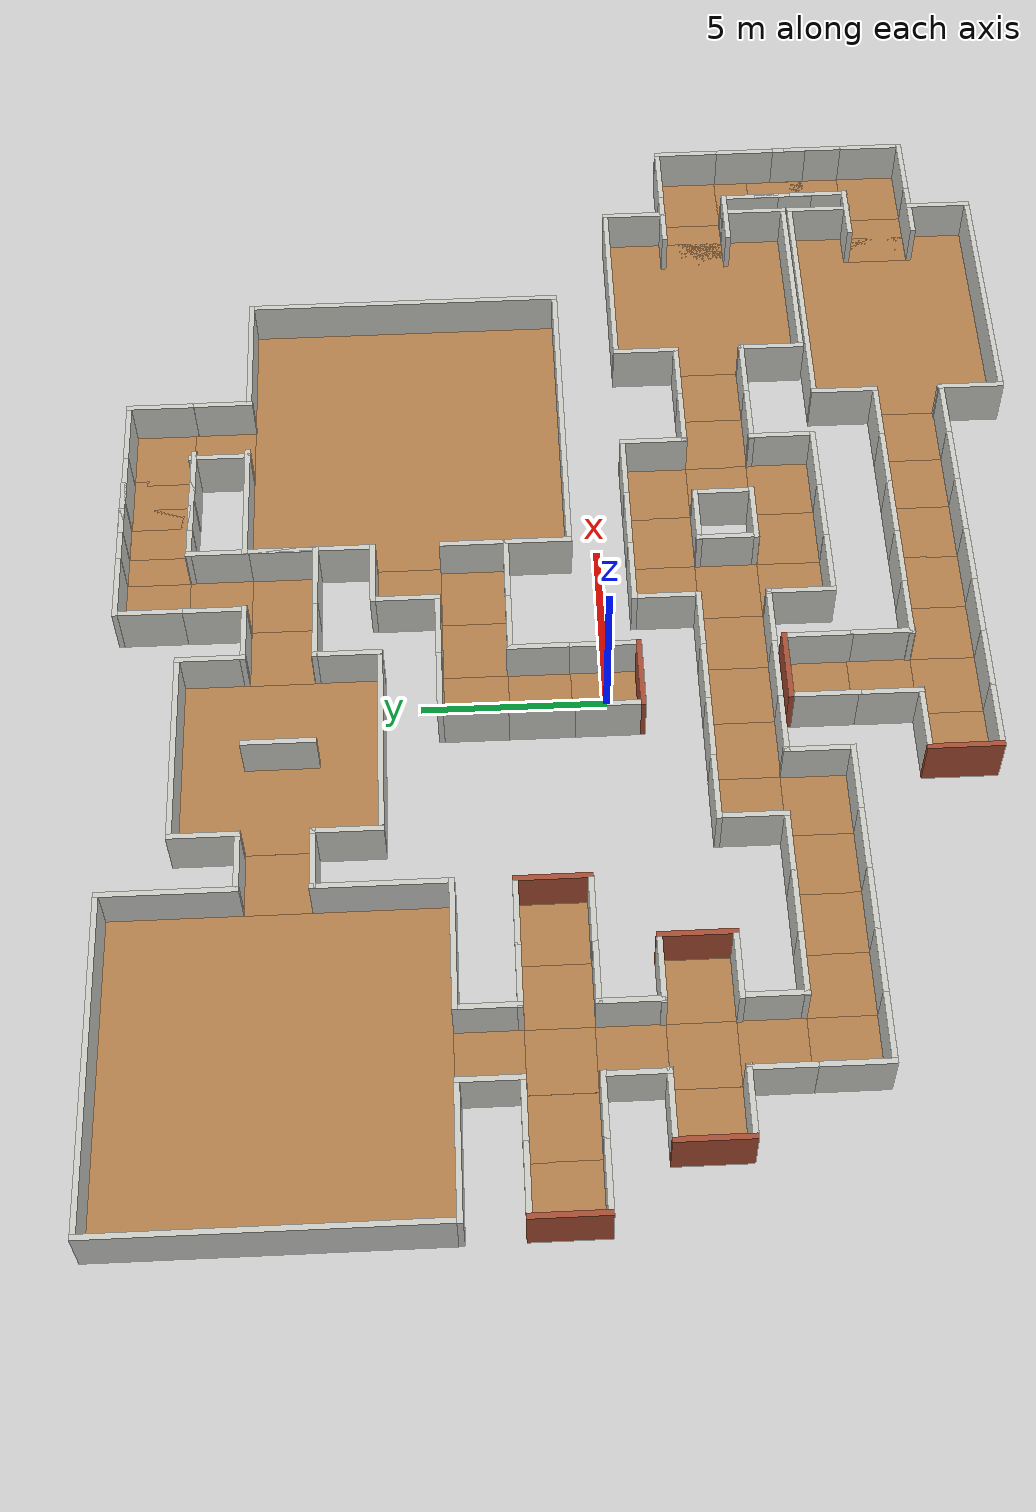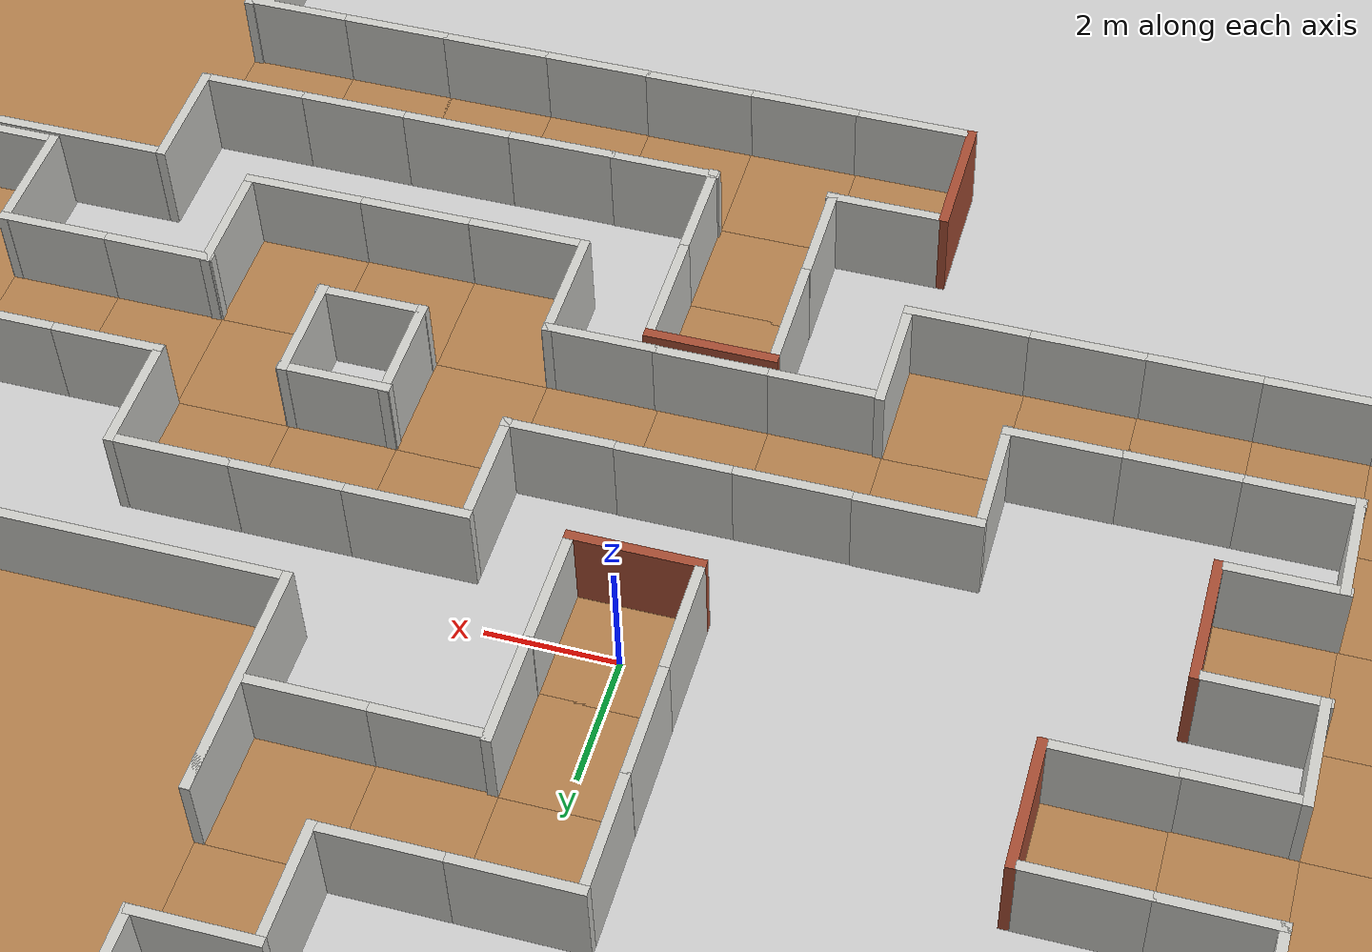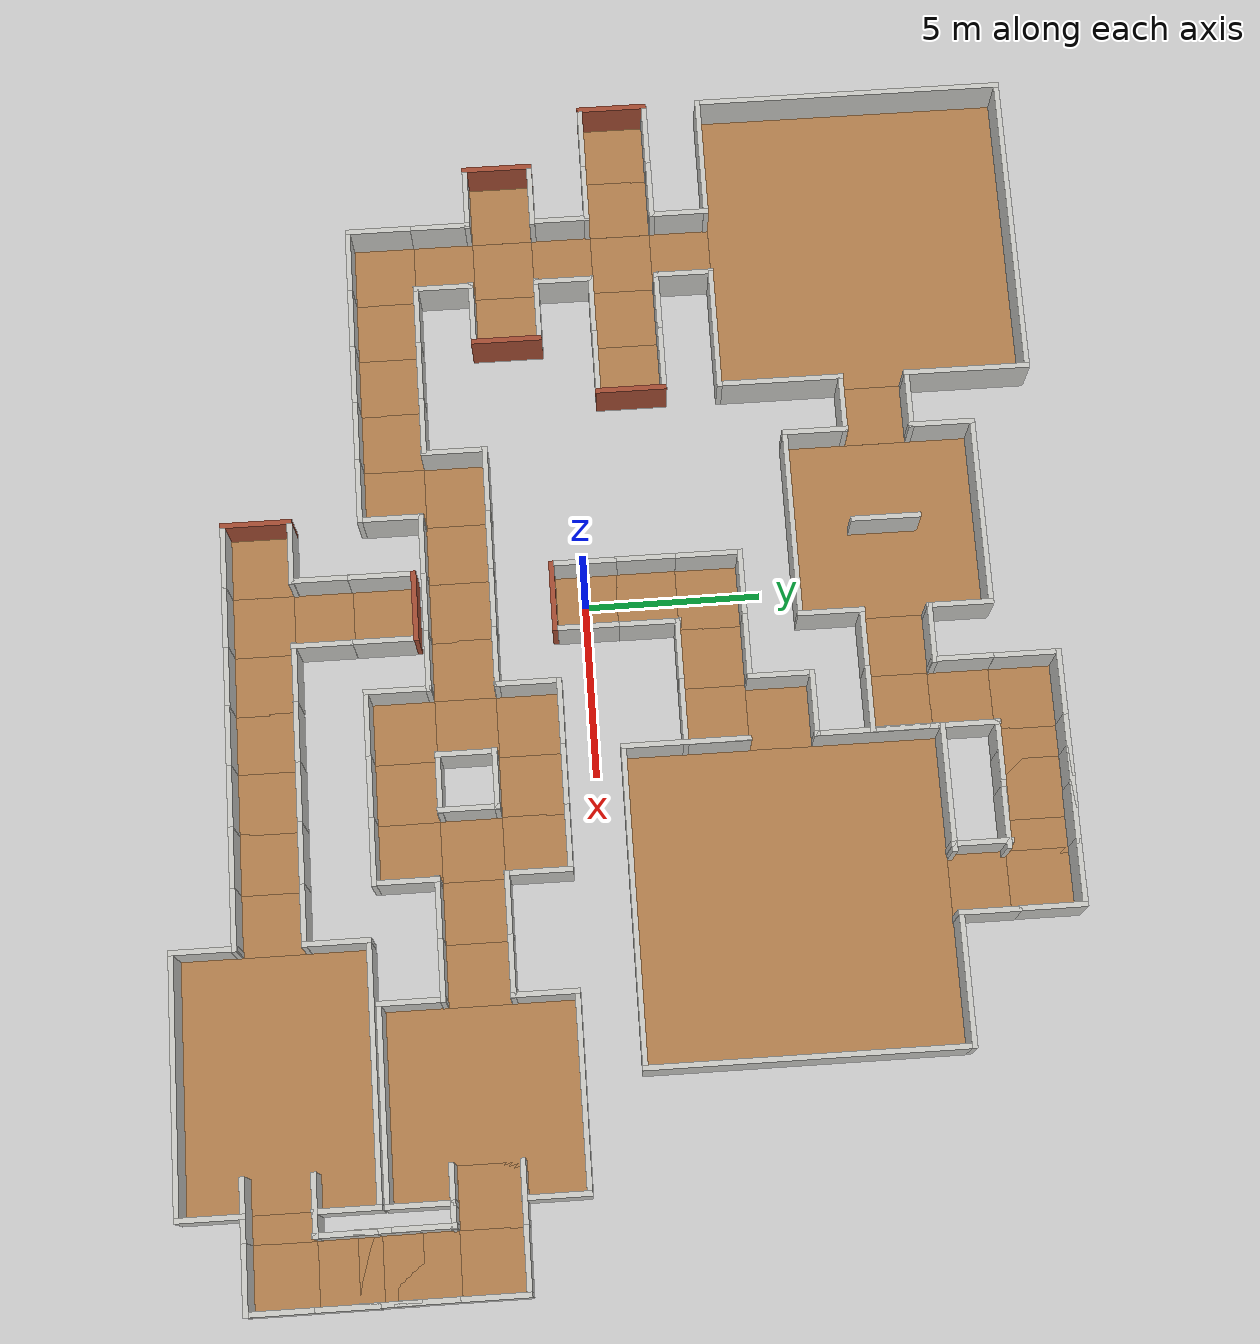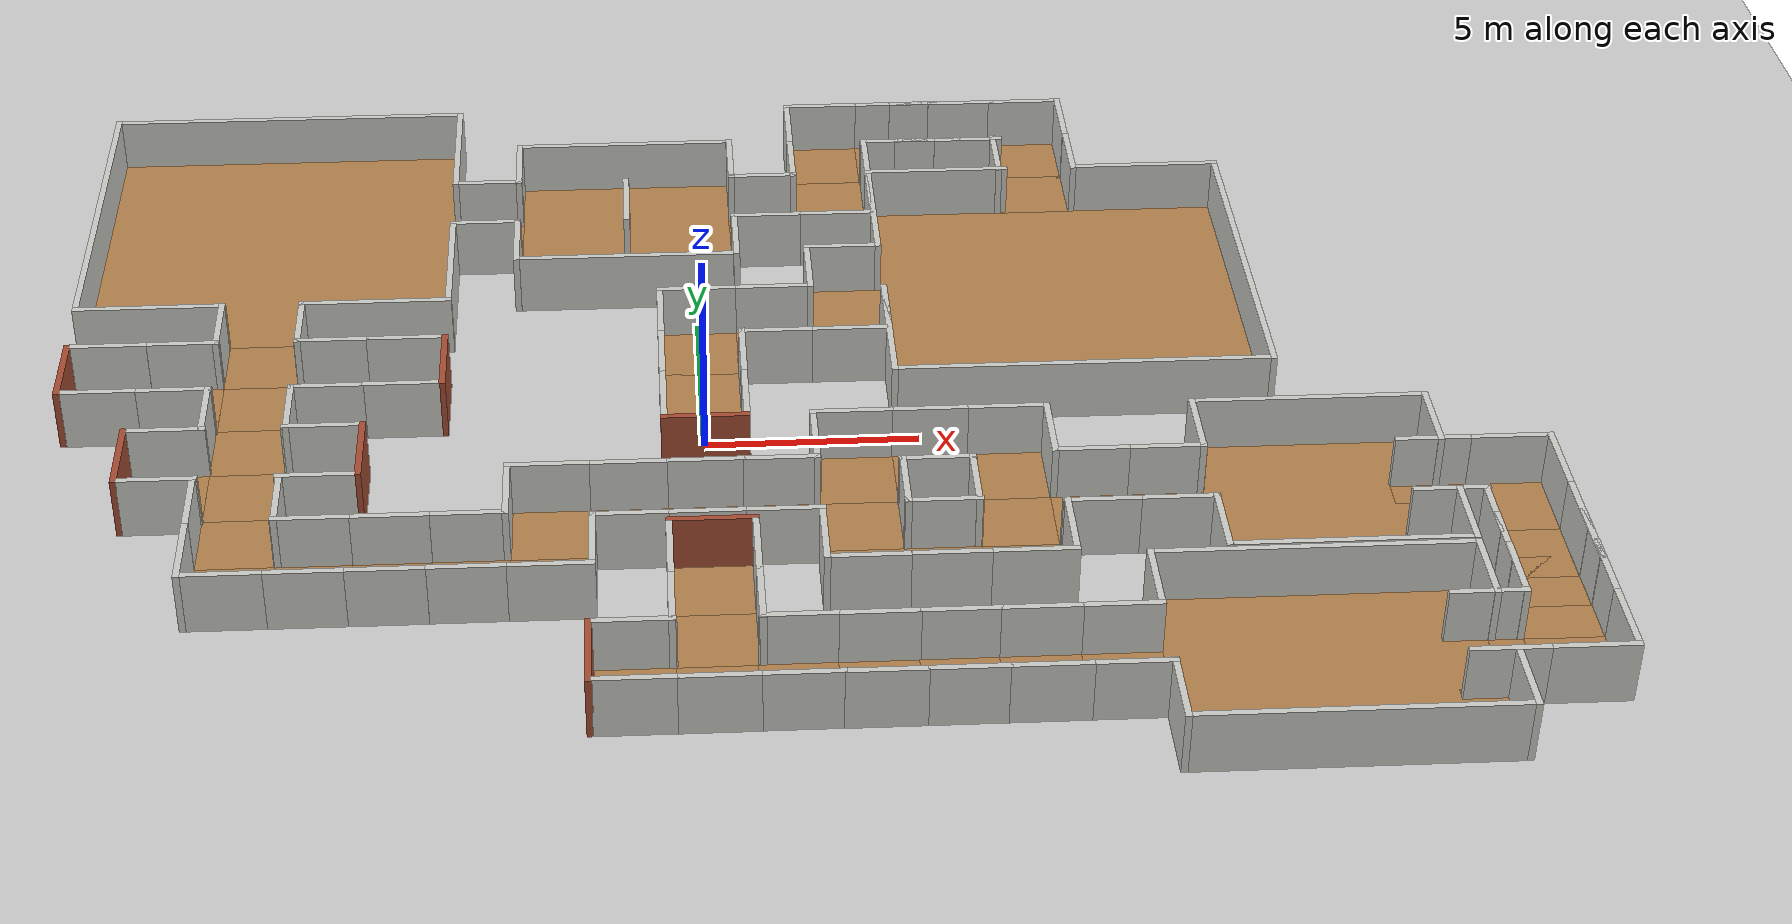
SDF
<sdf version="1.6">
 <world name="default">
  <light name="sun" type="directional">
   <pose>0 0 10 0 -0 0</pose>
   <diffuse>0.8 0.8 0.8 1</diffuse>
   <specular>0.1 0.1 0.1 1</specular>
   <attenuation>
    <range>1000</range>
    <constant>0.9</constant>
    <linear>0.01</linear>
    <quadratic>0.001</quadratic>
   </attenuation>
   <direction>-0.5 0.5 -1</direction>
  </light>
  <model name="ground_plane">
   <static>1</static>
   <link name="link">
    <collision name="collision">
     <geometry><plane><normal>0 0 1</normal><size>100 100</size></plane></geometry>
     <surface><friction><ode><mu>100</mu><mu2>50</mu2></ode></friction></surface>
    </collision>
    <visual name="visual">
     <cast_shadows>0</cast_shadows>
     <geometry><plane><normal>0 0 1</normal><size>100 100</size></plane></geometry>
     <material>
      <script><uri>file://media/materials/scripts/gazebo.material</uri><name>Gazebo/Grey</name></script>
     </material>
    </visual>
   </link>
  </model>
  <gravity>0 0 -9.8</gravity>
  <magnetic_field>6e-06 2.3e-05 -4.2e-05</magnetic_field>
  <atmosphere type="adiabatic"/>
  <physics name="default_physics" default="0" type="ode">
   <max_step_size>0.001</max_step_size>
   <real_time_factor>1</real_time_factor>
   <real_time_update_rate>1000</real_time_update_rate>
  </physics>
  <scene><ambient>0.4 0.4 0.4 1</ambient><background>0.7 0.7 0.7 1</background><shadows>1</shadows></scene>
  <spherical_coordinates>
   <surface_model>EARTH_WGS84</surface_model>
   <latitude_deg>0</latitude_deg>
   <longitude_deg>0</longitude_deg>
   <elevation>0</elevation>
   <heading_deg>0</heading_deg>
  </spherical_coordinates>
  <model name="nerve_end">
   <pose>0 0 0 0 0 -3.14159</pose>
   <link name="Wall_0">
    <collision name="Wall_0_Collision">
     <geometry><box><size>1.76 1.75 0.2</size></box></geometry>
     <pose>0 0 0.1 0 -0 0</pose>
    </collision>
    <visual name="Wall_0_Visual">
     <pose>0 0 0.1 0 -0 0</pose>
     <geometry><box><size>1.76 1.75 0.2</size></box></geometry>
     <material>
      <script><uri>file://media/materials/scripts/gazebo.material</uri><name>Gazebo/Wood</name></script>
      <ambient>1 0.764706 0.305882 1</ambient>
     </material>
    </visual>
    <pose>-0.009 -0.064 0 0 -0 0</pose>
   </link>
   <link name="Wall_2">
    <collision name="Wall_2_Collision">
     <geometry><box><size>1.8 0.15 1.5</size></box></geometry>
     <pose>0 0 0.75 0 -0 0</pose>
    </collision>
    <visual name="Wall_2_Visual">
     <pose>0 0 0.75 0 -0 0</pose>
     <geometry><box><size>1.8 0.15 1.5</size></box></geometry>
     <material>
      <script><uri>file://media/materials/scripts/gazebo.material</uri><name>Gazebo/CeilingTiled</name></script>
      <ambient>1 0.764706 0.305882 1</ambient>
     </material>
    </visual>
    <pose>-0.95 -0.065 0 0 0 -1.5708</pose>
   </link>
   <link name="Wall_4">
    <collision name="Wall_4_Collision">
     <geometry><box><size>1.8 0.15 1.5</size></box></geometry>
     <pose>0 0 0.75 0 -0 0</pose>
    </collision>
    <visual name="Wall_4_Visual">
     <pose>0 0 0.75 0 -0 0</pose>
     <geometry><box><size>1.8 0.15 1.5</size></box></geometry>
     <material>
      <script><uri>file://media/materials/scripts/gazebo.material</uri><name>Gazebo/CeilingTiled</name></script>
      <ambient>1 0.764706 0.305882 1</ambient>
     </material>
    </visual>
    <pose>0.95 -0.065 0 0 0 -1.5708</pose>
   </link>
   <link name="Wall_6">
    <collision name="Wall_6_Collision">
     <geometry><box><size>2.05 0.15 1.5</size></box></geometry>
     <pose>0 0 0.75 0 -0 0</pose>
    </collision>
    <visual name="Wall_6_Visual">
     <pose>0 0 0.75 0 -0 0</pose>
     <geometry><box><size>2.05 0.15 1.5</size></box></geometry>
     <material>
      <script><uri>file://media/materials/scripts/gazebo.material</uri><name>Gazebo/Bricks</name></script>
      <ambient>0.996078 0.47451 0.0196078 1</ambient>
     </material>
    </visual>
    <pose>0 0.89 0 0 -0 0</pose>
   </link>
   <static>1</static>
  </model>
  <model name="nerve_end_clone">
   <pose>0.033954 -5.68438 0 0 -0 2e-06</pose>
   <link name="Wall_0">
    <collision name="Wall_0_Collision">
     <geometry><box><size>1.76 1.75 0.2</size></box></geometry>
     <pose>0 0 0.1 0 -0 0</pose>
    </collision>
    <visual name="Wall_0_Visual">
     <pose>0 0 0.1 0 -0 0</pose>
     <geometry><box><size>1.76 1.75 0.2</size></box></geometry>
     <material>
      <script><uri>file://media/materials/scripts/gazebo.material</uri><name>Gazebo/Wood</name></script>
      <ambient>1 0.764706 0.305882 1</ambient>
     </material>
    </visual>
    <pose>-0.009 -0.064 0 0 -0 0</pose>
   </link>
   <link name="Wall_2">
    <collision name="Wall_2_Collision">
     <geometry><box><size>1.8 0.15 1.5</size></box></geometry>
     <pose>0 0 0.75 0 -0 0</pose>
    </collision>
    <visual name="Wall_2_Visual">
     <pose>0 0 0.75 0 -0 0</pose>
     <geometry><box><size>1.8 0.15 1.5</size></box></geometry>
     <material>
      <script><uri>file://media/materials/scripts/gazebo.material</uri><name>Gazebo/CeilingTiled</name></script>
      <ambient>1 0.764706 0.305882 1</ambient>
     </material>
    </visual>
    <pose>-0.95 -0.065 0 0 0 -1.5708</pose>
   </link>
   <link name="Wall_4">
    <collision name="Wall_4_Collision">
     <geometry><box><size>1.8 0.15 1.5</size></box></geometry>
     <pose>0 0 0.75 0 -0 0</pose>
    </collision>
    <visual name="Wall_4_Visual">
     <pose>0 0 0.75 0 -0 0</pose>
     <geometry><box><size>1.8 0.15 1.5</size></box></geometry>
     <material>
      <script><uri>file://media/materials/scripts/gazebo.material</uri><name>Gazebo/CeilingTiled</name></script>
      <ambient>1 0.764706 0.305882 1</ambient>
     </material>
    </visual>
    <pose>0.95 -0.065 0 0 0 -1.5708</pose>
   </link>
   <link name="Wall_6">
    <collision name="Wall_6_Collision">
     <geometry><box><size>2.05 0.15 1.5</size></box></geometry>
     <pose>0 0 0.75 0 -0 0</pose>
    </collision>
    <visual name="Wall_6_Visual">
     <pose>0 0 0.75 0 -0 0</pose>
     <geometry><box><size>2.05 0.15 1.5</size></box></geometry>
     <material>
      <script><uri>file://media/materials/scripts/gazebo.material</uri><name>Gazebo/Bricks</name></script>
      <ambient>0.996078 0.47451 0.0196078 1</ambient>
     </material>
    </visual>
    <pose>0 0.89 0 0 -0 0</pose>
   </link>
   <static>1</static>
  </model>
  <model name="nerve_straight">
   <pose>-1.7845 -3.55503 0 0 0 -1.5708</pose>
   <link name="Wall_0">
    <collision name="Wall_0_Collision">
     <geometry><box><size>1.76 1.75 0.2</size></box></geometry>
     <pose>0 0 0.1 0 -0 0</pose>
    </collision>
    <visual name="Wall_0_Visual">
     <pose>0 0 0.1 0 -0 0</pose>
     <geometry><box><size>1.76 1.75 0.2</size></box></geometry>
     <material>
      <script><uri>file://media/materials/scripts/gazebo.material</uri><name>Gazebo/Wood</name></script>
      <ambient>1 0.764706 0.305882 1</ambient>
     </material>
    </visual>
    <pose>0.005 -0.002 0 0 -0 3.14159</pose>
   </link>
   <link name="Wall_2">
    <collision name="Wall_2_Collision">
     <geometry><box><size>1.75 0.15 1.5</size></box></geometry>
     <pose>0 0 0.75 0 -0 0</pose>
    </collision>
    <visual name="Wall_2_Visual">
     <pose>0 0 0.75 0 -0 0</pose>
     <geometry><box><size>1.75 0.15 1.5</size></box></geometry>
     <material>
      <script><uri>file://media/materials/scripts/gazebo.material</uri><name>Gazebo/CeilingTiled</name></script>
      <ambient>1 0.764706 0.305882 1</ambient>
     </material>
    </visual>
    <pose>-0.955 0.002 0 0 0 -1.5708</pose>
   </link>
   <link name="Wall_4">
    <collision name="Wall_4_Collision">
     <geometry><box><size>1.75 0.15 1.5</size></box></geometry>
     <pose>0 0 0.75 0 -0 0</pose>
    </collision>
    <visual name="Wall_4_Visual">
     <pose>0 0 0.75 0 -0 0</pose>
     <geometry><box><size>1.75 0.15 1.5</size></box></geometry>
     <material>
      <script><uri>file://media/materials/scripts/gazebo.material</uri><name>Gazebo/CeilingTiled</name></script>
      <ambient>1 0.764706 0.305882 1</ambient>
     </material>
    </visual>
    <pose>0.955 0.002 0 0 0 -1.5708</pose>
   </link>
   <static>1</static>
  </model>
  <model name="nerve_straight_clone">
   <pose>-0.046085 -3.55479 0 0 0 -1.5708</pose>
   <link name="Wall_0">
    <collision name="Wall_0_Collision">
     <geometry><box><size>1.76 1.75 0.2</size></box></geometry>
     <pose>0 0 0.1 0 -0 0</pose>
    </collision>
    <visual name="Wall_0_Visual">
     <pose>0 0 0.1 0 -0 0</pose>
     <geometry><box><size>1.76 1.75 0.2</size></box></geometry>
     <material>
      <script><uri>file://media/materials/scripts/gazebo.material</uri><name>Gazebo/Wood</name></script>
      <ambient>1 0.764706 0.305882 1</ambient>
     </material>
    </visual>
    <pose>0.005 -0.002 0 0 -0 3.14159</pose>
   </link>
   <link name="Wall_2">
    <collision name="Wall_2_Collision">
     <geometry><box><size>1.75 0.15 1.5</size></box></geometry>
     <pose>0 0 0.75 0 -0 0</pose>
    </collision>
    <visual name="Wall_2_Visual">
     <pose>0 0 0.75 0 -0 0</pose>
     <geometry><box><size>1.75 0.15 1.5</size></box></geometry>
     <material>
      <script><uri>file://media/materials/scripts/gazebo.material</uri><name>Gazebo/CeilingTiled</name></script>
      <ambient>1 0.764706 0.305882 1</ambient>
     </material>
    </visual>
    <pose>-0.955 0.002 0 0 0 -1.5708</pose>
   </link>
   <link name="Wall_4">
    <collision name="Wall_4_Collision">
     <geometry><box><size>1.75 0.15 1.5</size></box></geometry>
     <pose>0 0 0.75 0 -0 0</pose>
    </collision>
    <visual name="Wall_4_Visual">
     <pose>0 0 0.75 0 -0 0</pose>
     <geometry><box><size>1.75 0.15 1.5</size></box></geometry>
     <material>
      <script><uri>file://media/materials/scripts/gazebo.material</uri><name>Gazebo/CeilingTiled</name></script>
      <ambient>1 0.764706 0.305882 1</ambient>
     </material>
    </visual>
    <pose>0.955 0.002 0 0 0 -1.5708</pose>
   </link>
   <static>1</static>
  </model>
  <model name="nerve_straight_clone_0">
   <pose>-5.29676 -5.28219 0 0 0 -1.5708</pose>
   <link name="Wall_0">
    <collision name="Wall_0_Collision">
     <geometry><box><size>1.76 1.75 0.2</size></box></geometry>
     <pose>0 0 0.1 0 -0 0</pose>
    </collision>
    <visual name="Wall_0_Visual">
     <pose>0 0 0.1 0 -0 0</pose>
     <geometry><box><size>1.76 1.75 0.2</size></box></geometry>
     <material>
      <script><uri>file://media/materials/scripts/gazebo.material</uri><name>Gazebo/Wood</name></script>
      <ambient>1 0.764706 0.305882 1</ambient>
     </material>
    </visual>
    <pose>0.005 -0.002 0 0 -0 3.14159</pose>
   </link>
   <link name="Wall_2">
    <collision name="Wall_2_Collision">
     <geometry><box><size>1.75 0.15 1.5</size></box></geometry>
     <pose>0 0 0.75 0 -0 0</pose>
    </collision>
    <visual name="Wall_2_Visual">
     <pose>0 0 0.75 0 -0 0</pose>
     <geometry><box><size>1.75 0.15 1.5</size></box></geometry>
     <material>
      <script><uri>file://media/materials/scripts/gazebo.material</uri><name>Gazebo/CeilingTiled</name></script>
      <ambient>1 0.764706 0.305882 1</ambient>
     </material>
    </visual>
    <pose>-0.955 0.002 0 0 0 -1.5708</pose>
   </link>
   <link name="Wall_4">
    <collision name="Wall_4_Collision">
     <geometry><box><size>1.75 0.15 1.5</size></box></geometry>
     <pose>0 0 0.75 0 -0 0</pose>
    </collision>
    <visual name="Wall_4_Visual">
     <pose>0 0 0.75 0 -0 0</pose>
     <geometry><box><size>1.75 0.15 1.5</size></box></geometry>
     <material>
      <script><uri>file://media/materials/scripts/gazebo.material</uri><name>Gazebo/CeilingTiled</name></script>
      <ambient>1 0.764706 0.305882 1</ambient>
     </material>
    </visual>
    <pose>0.955 0.002 0 0 0 -1.5708</pose>
   </link>
   <static>1</static>
  </model>
  <model name="nerve_straight_clone_0_clone_clone">
   <pose>0.002128 1.78513 0 0 -0 3.14159</pose>
   <link name="Wall_0">
    <collision name="Wall_0_Collision">
     <geometry><box><size>1.76 1.75 0.2</size></box></geometry>
     <pose>0 0 0.1 0 -0 0</pose>
    </collision>
    <visual name="Wall_0_Visual">
     <pose>0 0 0.1 0 -0 0</pose>
     <geometry><box><size>1.76 1.75 0.2</size></box></geometry>
     <material>
      <script><uri>file://media/materials/scripts/gazebo.material</uri><name>Gazebo/Wood</name></script>
      <ambient>1 0.764706 0.305882 1</ambient>
     </material>
    </visual>
    <pose>0.005 -0.002 0 0 -0 3.14159</pose>
   </link>
   <link name="Wall_2">
    <collision name="Wall_2_Collision">
     <geometry><box><size>1.75 0.15 1.5</size></box></geometry>
     <pose>0 0 0.75 0 -0 0</pose>
    </collision>
    <visual name="Wall_2_Visual">
     <pose>0 0 0.75 0 -0 0</pose>
     <geometry><box><size>1.75 0.15 1.5</size></box></geometry>
     <material>
      <script><uri>file://media/materials/scripts/gazebo.material</uri><name>Gazebo/CeilingTiled</name></script>
      <ambient>1 0.764706 0.305882 1</ambient>
     </material>
    </visual>
    <pose>-0.955 0.002 0 0 0 -1.5708</pose>
   </link>
   <link name="Wall_4">
    <collision name="Wall_4_Collision">
     <geometry><box><size>1.75 0.15 1.5</size></box></geometry>
     <pose>0 0 0.75 0 -0 0</pose>
    </collision>
    <visual name="Wall_4_Visual">
     <pose>0 0 0.75 0 -0 0</pose>
     <geometry><box><size>1.75 0.15 1.5</size></box></geometry>
     <material>
      <script><uri>file://media/materials/scripts/gazebo.material</uri><name>Gazebo/CeilingTiled</name></script>
      <ambient>1 0.764706 0.305882 1</ambient>
     </material>
    </visual>
    <pose>0.955 0.002 0 0 0 -1.5708</pose>
   </link>
   <static>1</static>
  </model>
  <model name="nerve_room_5x5ARENA_right">
   <pose>-10.4798 8.71778 0 0 -0 1.57</pose>
   <link name="Wall_11">
    <collision name="Wall_11_Collision">
     <geometry><box><size>8.75 0.15 1.5</size></box></geometry>
     <pose>0 0 0.75 0 -0 0</pose>
    </collision>
    <visual name="Wall_11_Visual">
     <pose>0 0 0.75 0 -0 0</pose>
     <geometry><box><size>8.75 0.15 1.5</size></box></geometry>
     <material>
      <script><uri>file://media/materials/scripts/gazebo.material</uri><name>Gazebo/CeilingTiled</name></script>
      <ambient>1 0.764706 0.305882 1</ambient>
     </material>
    </visual>
    <pose>4.44912 -0.000431 0 0 0 -1.5708</pose>
   </link>
   <link name="Wall_13">
    <collision name="Wall_13_Collision">
     <geometry><box><size>3.65 0.15 1.5</size></box></geometry>
     <pose>0 0 0.75 0 -0 0</pose>
    </collision>
    <visual name="Wall_13_Visual">
     <pose>0 0 0.75 0 -0 0</pose>
     <geometry><box><size>3.65 0.15 1.5</size></box></geometry>
     <material>
      <script><uri>file://media/materials/scripts/gazebo.material</uri><name>Gazebo/CeilingTiled</name></script>
      <ambient>1 0.764706 0.305882 1</ambient>
     </material>
    </visual>
    <pose>-4.44961 2.70076 0 0 0 -1.5708</pose>
   </link>
   <link name="Wall_15">
    <collision name="Wall_15_Collision">
     <geometry><box><size>3.65 0.15 1.5</size></box></geometry>
     <pose>0 0 0.75 0 -0 0</pose>
    </collision>
    <visual name="Wall_15_Visual">
     <pose>0 0 0.75 0 -0 0</pose>
     <geometry><box><size>3.65 0.15 1.5</size></box></geometry>
     <material>
      <script><uri>file://media/materials/scripts/gazebo.material</uri><name>Gazebo/CeilingTiled</name></script>
      <ambient>1 0.764706 0.305882 1</ambient>
     </material>
    </visual>
    <pose>2.69961 -4.45076 0 0 -0 0</pose>
   </link>
   <link name="Wall_17">
    <collision name="Wall_17_Collision">
     <geometry><box><size>8.90028 0.15 1.5</size></box></geometry>
     <pose>0 0 0.75 0 -0 0</pose>
    </collision>
    <visual name="Wall_17_Visual">
     <pose>0 0 0.75 0 -0 0</pose>
     <geometry><box><size>8.90028 0.15 1.5</size></box></geometry>
     <material>
      <script><uri>file://media/materials/scripts/gazebo.material</uri><name>Gazebo/CeilingTiled</name></script>
      <ambient>1 0.764706 0.305882 1</ambient>
     </material>
    </visual>
    <pose>0.074346 4.45022 0 0 0 -6.5e-05</pose>
   </link>
   <link name="Wall_21">
    <collision name="Wall_21_Collision">
     <geometry><box><size>3.5 0.15 1.5</size></box></geometry>
     <pose>0 0 0.75 0 -0 0</pose>
    </collision>
    <visual name="Wall_21_Visual">
     <pose>0 0 0.75 0 -0 0</pose>
     <geometry><box><size>3.5 0.15 1.5</size></box></geometry>
     <material>
      <script><uri>file://media/materials/scripts/gazebo.material</uri><name>Gazebo/CeilingTiled</name></script>
      <ambient>1 0.764706 0.305882 1</ambient>
     </material>
    </visual>
    <pose>-2.62383 -4.4498 0 0 -0 0</pose>
   </link>
   <link name="Wall_25">
    <collision name="Wall_25_Collision">
     <geometry><box><size>3.65 0.15 1.5</size></box></geometry>
     <pose>0 0 0.75 0 -0 0</pose>
    </collision>
    <visual name="Wall_25_Visual">
     <pose>0 0 0.75 0 -0 0</pose>
     <geometry><box><size>3.65 0.15 1.5</size></box></geometry>
     <material>
      <script><uri>file://media/materials/scripts/gazebo.material</uri><name>Gazebo/CeilingTiled</name></script>
      <ambient>1 0.764706 0.305882 1</ambient>
     </material>
    </visual>
    <pose>-4.44941 -2.70044 0 0 0 -1.5708</pose>
   </link>
   <link name="Wall_6">
    <collision name="Wall_6_Collision">
     <geometry><box><size>8.76 8.75 0.2</size></box></geometry>
     <pose>0 0 0.1 0 -0 0</pose>
    </collision>
    <visual name="Wall_6_Visual">
     <pose>0 0 0.1 0 -0 0</pose>
     <geometry><box><size>8.76 8.75 0.2</size></box></geometry>
     <material>
      <script><uri>file://media/materials/scripts/gazebo.material</uri><name>Gazebo/Wood</name></script>
      <ambient>1 0.764706 0.305882 1</ambient>
     </material>
    </visual>
    <pose>0.000485 -0.004173 0 0 -0 1.5708</pose>
   </link>
   <static>1</static>
  </model>
  <model name="nerve_straight_clone_0_clone_clone_0">
   <pose>-10.4881 3.47237 0 0 -0 3.14159</pose>
   <link name="Wall_0">
    <collision name="Wall_0_Collision">
     <geometry><box><size>1.76 1.75 0.2</size></box></geometry>
     <pose>0 0 0.1 0 -0 0</pose>
    </collision>
    <visual name="Wall_0_Visual">
     <pose>0 0 0.1 0 -0 0</pose>
     <geometry><box><size>1.76 1.75 0.2</size></box></geometry>
     <material>
      <script><uri>file://media/materials/scripts/gazebo.material</uri><name>Gazebo/Wood</name></script>
      <ambient>1 0.764706 0.305882 1</ambient>
     </material>
    </visual>
    <pose>0.005 -0.002 0 0 -0 3.14159</pose>
   </link>
   <link name="Wall_2">
    <collision name="Wall_2_Collision">
     <geometry><box><size>1.75 0.15 1.5</size></box></geometry>
     <pose>0 0 0.75 0 -0 0</pose>
    </collision>
    <visual name="Wall_2_Visual">
     <pose>0 0 0.75 0 -0 0</pose>
     <geometry><box><size>1.75 0.15 1.5</size></box></geometry>
     <material>
      <script><uri>file://media/materials/scripts/gazebo.material</uri><name>Gazebo/CeilingTiled</name></script>
      <ambient>1 0.764706 0.305882 1</ambient>
     </material>
    </visual>
    <pose>-0.955 0.002 0 0 0 -1.5708</pose>
   </link>
   <link name="Wall_4">
    <collision name="Wall_4_Collision">
     <geometry><box><size>1.75 0.15 1.5</size></box></geometry>
     <pose>0 0 0.75 0 -0 0</pose>
    </collision>
    <visual name="Wall_4_Visual">
     <pose>0 0 0.75 0 -0 0</pose>
     <geometry><box><size>1.75 0.15 1.5</size></box></geometry>
     <material>
      <script><uri>file://media/materials/scripts/gazebo.material</uri><name>Gazebo/CeilingTiled</name></script>
      <ambient>1 0.764706 0.305882 1</ambient>
     </material>
    </visual>
    <pose>0.955 0.002 0 0 0 -1.5708</pose>
   </link>
   <static>1</static>
  </model>
  <model name="nerve_room_3x4">
   <pose>12.9907 -9.16928 0 0 -0 1.5708</pose>
   <link name="Wall_11">
    <collision name="Wall_11_Collision">
     <geometry><box><size>7 0.15 1.5</size></box></geometry>
     <pose>0 0 0.75 0 -0 0</pose>
    </collision>
    <visual name="Wall_11_Visual">
     <pose>0 0 0.75 0 -0 0</pose>
     <geometry><box><size>7 0.15 1.5</size></box></geometry>
     <material>
      <script><uri>file://media/materials/scripts/gazebo.material</uri><name>Gazebo/CeilingTiled</name></script>
      <ambient>1 0.764706 0.305882 1</ambient>
     </material>
    </visual>
    <pose>-2.69862 -0.000423 0 0 0 -1.5708</pose>
   </link>
   <link name="Wall_13">
    <collision name="Wall_13_Collision">
     <geometry><box><size>7 0.15 1.5</size></box></geometry>
     <pose>0 0 0.75 0 -0 0</pose>
    </collision>
    <visual name="Wall_13_Visual">
     <pose>0 0 0.75 0 -0 0</pose>
     <geometry><box><size>7 0.15 1.5</size></box></geometry>
     <material>
      <script><uri>file://media/materials/scripts/gazebo.material</uri><name>Gazebo/CeilingTiled</name></script>
      <ambient>1 0.764706 0.305882 1</ambient>
     </material>
    </visual>
    <pose>2.69862 -0.000308 0 0 0 -1.5708</pose>
   </link>
   <link name="Wall_15">
    <collision name="Wall_15_Collision">
     <geometry><box><size>1.9 0.15 1.5</size></box></geometry>
     <pose>0 0 0.75 0 -0 0</pose>
    </collision>
    <visual name="Wall_15_Visual">
     <pose>0 0 0.75 0 -0 0</pose>
     <geometry><box><size>1.9 0.15 1.5</size></box></geometry>
     <material>
      <script><uri>file://media/materials/scripts/gazebo.material</uri><name>Gazebo/CeilingTiled</name></script>
      <ambient>1 0.764706 0.305882 1</ambient>
     </material>
    </visual>
    <pose>-1.82276 -3.57547 0 0 -0 0</pose>
   </link>
   <link name="Wall_17">
    <collision name="Wall_17_Collision">
     <geometry><box><size>1.9 0.15 1.5</size></box></geometry>
     <pose>0 0 0.75 0 -0 0</pose>
    </collision>
    <visual name="Wall_17_Visual">
     <pose>0 0 0.75 0 -0 0</pose>
     <geometry><box><size>1.9 0.15 1.5</size></box></geometry>
     <material>
      <script><uri>file://media/materials/scripts/gazebo.material</uri><name>Gazebo/CeilingTiled</name></script>
      <ambient>1 0.764706 0.305882 1</ambient>
     </material>
    </visual>
    <pose>-1.82217 3.57448 0 0 -0 0</pose>
   </link>
   <link name="Wall_19">
    <collision name="Wall_19_Collision">
     <geometry><box><size>1.9 0.15 1.5</size></box></geometry>
     <pose>0 0 0.75 0 -0 0</pose>
    </collision>
    <visual name="Wall_19_Visual">
     <pose>0 0 0.75 0 -0 0</pose>
     <geometry><box><size>1.9 0.15 1.5</size></box></geometry>
     <material>
      <script><uri>file://media/materials/scripts/gazebo.material</uri><name>Gazebo/CeilingTiled</name></script>
      <ambient>1 0.764706 0.305882 1</ambient>
     </material>
    </visual>
    <pose>1.82197 3.57547 0 0 -0 0</pose>
   </link>
   <link name="Wall_21">
    <collision name="Wall_21_Collision">
     <geometry><box><size>1.9 0.15 1.5</size></box></geometry>
     <pose>0 0 0.75 0 -0 0</pose>
    </collision>
    <visual name="Wall_21_Visual">
     <pose>0 0 0.75 0 -0 0</pose>
     <geometry><box><size>1.9 0.15 1.5</size></box></geometry>
     <material>
      <script><uri>file://media/materials/scripts/gazebo.material</uri><name>Gazebo/CeilingTiled</name></script>
      <ambient>1 0.764706 0.305882 1</ambient>
     </material>
    </visual>
    <pose>1.82281 -3.57503 0 0 -0 0</pose>
   </link>
   <link name="Wall_6">
    <collision name="Wall_6_Collision">
     <geometry><box><size>7 5.25 0.2</size></box></geometry>
     <pose>0 0 0.1 0 -0 0</pose>
    </collision>
    <visual name="Wall_6_Visual">
     <pose>0 0 0.1 0 -0 0</pose>
     <geometry><box><size>7 5.25 0.2</size></box></geometry>
     <material>
      <script><uri>file://media/materials/scripts/gazebo.material</uri><name>Gazebo/Wood</name></script>
      <ambient>1 0.764706 0.305882 1</ambient>
     </material>
    </visual>
    <pose>-0.001169 -0.000255 0 0 -0 1.5708</pose>
   </link>
   <static>1</static>
  </model>
  <model name="nerve_room_3x3_split">
   <pose>-1.72967 8.71627 0 0 0 -1.57079</pose>
   <link name="Wall_11">
    <collision name="Wall_11_Collision">
     <geometry><box><size>5.25 0.15 1.5</size></box></geometry>
     <pose>0 0 0.75 0 -0 0</pose>
    </collision>
    <visual name="Wall_11_Visual">
     <pose>0 0 0.75 0 -0 0</pose>
     <geometry><box><size>5.25 0.15 1.5</size></box></geometry>
     <material>
      <script><uri>file://media/materials/scripts/gazebo.material</uri><name>Gazebo/CeilingTiled</name></script>
      <ambient>1 0.764706 0.305882 1</ambient>
     </material>
    </visual>
    <pose>-2.69653 -0.003278 0 0 0 -1.5708</pose>
   </link>
   <link name="Wall_13">
    <collision name="Wall_13_Collision">
     <geometry><box><size>5.25 0.15 1.5</size></box></geometry>
     <pose>0 0 0.75 0 -0 0</pose>
    </collision>
    <visual name="Wall_13_Visual">
     <pose>0 0 0.75 0 -0 0</pose>
     <geometry><box><size>5.25 0.15 1.5</size></box></geometry>
     <material>
      <script><uri>file://media/materials/scripts/gazebo.material</uri><name>Gazebo/CeilingTiled</name></script>
      <ambient>1 0.764706 0.305882 1</ambient>
     </material>
    </visual>
    <pose>2.69688 -0.000452 0 0 0 -1.5708</pose>
   </link>
   <link name="Wall_15">
    <collision name="Wall_15_Collision">
     <geometry><box><size>1.9 0.15 1.5</size></box></geometry>
     <pose>0 0 0.75 0 -0 0</pose>
    </collision>
    <visual name="Wall_15_Visual">
     <pose>0 0 0.75 0 -0 0</pose>
     <geometry><box><size>1.9 0.15 1.5</size></box></geometry>
     <material>
      <script><uri>file://media/materials/scripts/gazebo.material</uri><name>Gazebo/CeilingTiled</name></script>
      <ambient>1 0.764706 0.305882 1</ambient>
     </material>
    </visual>
    <pose>-1.82279 -2.70217 0 0 -0 0</pose>
   </link>
   <link name="Wall_17">
    <collision name="Wall_17_Collision">
     <geometry><box><size>1.9 0.15 1.5</size></box></geometry>
     <pose>0 0 0.75 0 -0 0</pose>
    </collision>
    <visual name="Wall_17_Visual">
     <pose>0 0 0.75 0 -0 0</pose>
     <geometry><box><size>1.9 0.15 1.5</size></box></geometry>
     <material>
      <script><uri>file://media/materials/scripts/gazebo.material</uri><name>Gazebo/CeilingTiled</name></script>
      <ambient>1 0.764706 0.305882 1</ambient>
     </material>
    </visual>
    <pose>-1.82219 2.69878 0 0 -0 0</pose>
   </link>
   <link name="Wall_19">
    <collision name="Wall_19_Collision">
     <geometry><box><size>1.9 0.15 1.5</size></box></geometry>
     <pose>0 0 0.75 0 -0 0</pose>
    </collision>
    <visual name="Wall_19_Visual">
     <pose>0 0 0.75 0 -0 0</pose>
     <geometry><box><size>1.9 0.15 1.5</size></box></geometry>
     <material>
      <script><uri>file://media/materials/scripts/gazebo.material</uri><name>Gazebo/CeilingTiled</name></script>
      <ambient>1 0.764706 0.305882 1</ambient>
     </material>
    </visual>
    <pose>1.82194 2.70217 0 0 -0 0</pose>
   </link>
   <link name="Wall_21">
    <collision name="Wall_21_Collision">
     <geometry><box><size>1.9 0.15 1.5</size></box></geometry>
     <pose>0 0 0.75 0 -0 0</pose>
    </collision>
    <visual name="Wall_21_Visual">
     <pose>0 0 0.75 0 -0 0</pose>
     <geometry><box><size>1.9 0.15 1.5</size></box></geometry>
     <material>
      <script><uri>file://media/materials/scripts/gazebo.material</uri><name>Gazebo/CeilingTiled</name></script>
      <ambient>1 0.764706 0.305882 1</ambient>
     </material>
    </visual>
    <pose>1.82279 -2.70173 0 0 -0 0</pose>
   </link>
   <link name="Wall_23">
    <collision name="Wall_23_Collision">
     <geometry><box><size>2 0.15 1.5</size></box></geometry>
     <pose>0 0 0.75 0 -0 0</pose>
    </collision>
    <visual name="Wall_23_Visual">
     <pose>0 0 0.75 0 -0 0</pose>
     <geometry><box><size>2 0.15 1.5</size></box></geometry>
     <material>
      <script><uri>file://media/materials/scripts/gazebo.material</uri><name>Gazebo/CeilingTiled</name></script>
      <ambient>1 0.764706 0.305882 1</ambient>
     </material>
    </visual>
    <pose>0.033144 0.01482 0 0 -0 0</pose>
   </link>
   <link name="Wall_6">
    <collision name="Wall_6_Collision">
     <geometry><box><size>5.26 5.25 0.2</size></box></geometry>
     <pose>0 0 0.1 0 -0 0</pose>
    </collision>
    <visual name="Wall_6_Visual">
     <pose>0 0 0.1 0 -0 0</pose>
     <geometry><box><size>5.26 5.25 0.2</size></box></geometry>
     <material>
      <script><uri>file://media/materials/scripts/gazebo.material</uri><name>Gazebo/Wood</name></script>
      <ambient>1 0.764706 0.305882 1</ambient>
     </material>
    </visual>
    <pose>-0.001194 0.003047 0 0 -0 1.5708</pose>
   </link>
   <static>1</static>
  </model>
  <model name="nerve_room_3x3">
   <pose>13.8713 -3.57836 0 0 0 -1.57079</pose>
   <link name="Wall_11">
    <collision name="Wall_11_Collision">
     <geometry><box><size>5.25 0.15 1.5</size></box></geometry>
     <pose>0 0 0.75 0 -0 0</pose>
    </collision>
    <visual name="Wall_11_Visual">
     <pose>0 0 0.75 0 -0 0</pose>
     <geometry><box><size>5.25 0.15 1.5</size></box></geometry>
     <material>
      <script><uri>file://media/materials/scripts/gazebo.material</uri><name>Gazebo/CeilingTiled</name></script>
      <ambient>1 0.764706 0.305882 1</ambient>
     </material>
    </visual>
    <pose>-2.69653 -0.003278 0 0 0 -1.5708</pose>
   </link>
   <link name="Wall_13">
    <collision name="Wall_13_Collision">
     <geometry><box><size>5.25 0.15 1.5</size></box></geometry>
     <pose>0 0 0.75 0 -0 0</pose>
    </collision>
    <visual name="Wall_13_Visual">
     <pose>0 0 0.75 0 -0 0</pose>
     <geometry><box><size>5.25 0.15 1.5</size></box></geometry>
     <material>
      <script><uri>file://media/materials/scripts/gazebo.material</uri><name>Gazebo/CeilingTiled</name></script>
      <ambient>1 0.764706 0.305882 1</ambient>
     </material>
    </visual>
    <pose>2.69688 -0.000452 0 0 0 -1.5708</pose>
   </link>
   <link name="Wall_15">
    <collision name="Wall_15_Collision">
     <geometry><box><size>1.9 0.15 1.5</size></box></geometry>
     <pose>0 0 0.75 0 -0 0</pose>
    </collision>
    <visual name="Wall_15_Visual">
     <pose>0 0 0.75 0 -0 0</pose>
     <geometry><box><size>1.9 0.15 1.5</size></box></geometry>
     <material>
      <script><uri>file://media/materials/scripts/gazebo.material</uri><name>Gazebo/CeilingTiled</name></script>
      <ambient>1 0.764706 0.305882 1</ambient>
     </material>
    </visual>
    <pose>-1.82279 -2.70217 0 0 -0 0</pose>
   </link>
   <link name="Wall_17">
    <collision name="Wall_17_Collision">
     <geometry><box><size>1.9 0.15 1.5</size></box></geometry>
     <pose>0 0 0.75 0 -0 0</pose>
    </collision>
    <visual name="Wall_17_Visual">
     <pose>0 0 0.75 0 -0 0</pose>
     <geometry><box><size>1.9 0.15 1.5</size></box></geometry>
     <material>
      <script><uri>file://media/materials/scripts/gazebo.material</uri><name>Gazebo/CeilingTiled</name></script>
      <ambient>1 0.764706 0.305882 1</ambient>
     </material>
    </visual>
    <pose>-1.82219 2.69878 0 0 -0 0</pose>
   </link>
   <link name="Wall_19">
    <collision name="Wall_19_Collision">
     <geometry><box><size>1.9 0.15 1.5</size></box></geometry>
     <pose>0 0 0.75 0 -0 0</pose>
    </collision>
    <visual name="Wall_19_Visual">
     <pose>0 0 0.75 0 -0 0</pose>
     <geometry><box><size>1.9 0.15 1.5</size></box></geometry>
     <material>
      <script><uri>file://media/materials/scripts/gazebo.material</uri><name>Gazebo/CeilingTiled</name></script>
      <ambient>1 0.764706 0.305882 1</ambient>
     </material>
    </visual>
    <pose>1.82194 2.70217 0 0 -0 0</pose>
   </link>
   <link name="Wall_21">
    <collision name="Wall_21_Collision">
     <geometry><box><size>1.9 0.15 1.5</size></box></geometry>
     <pose>0 0 0.75 0 -0 0</pose>
    </collision>
    <visual name="Wall_21_Visual">
     <pose>0 0 0.75 0 -0 0</pose>
     <geometry><box><size>1.9 0.15 1.5</size></box></geometry>
     <material>
      <script><uri>file://media/materials/scripts/gazebo.material</uri><name>Gazebo/CeilingTiled</name></script>
      <ambient>1 0.764706 0.305882 1</ambient>
     </material>
    </visual>
    <pose>1.82279 -2.70173 0 0 -0 0</pose>
   </link>
   <link name="Wall_6">
    <collision name="Wall_6_Collision">
     <geometry><box><size>5.26 5.25 0.2</size></box></geometry>
     <pose>0 0 0.1 0 -0 0</pose>
    </collision>
    <visual name="Wall_6_Visual">
     <pose>0 0 0.1 0 -0 0</pose>
     <geometry><box><size>5.26 5.25 0.2</size></box></geometry>
     <material>
      <script><uri>file://media/materials/scripts/gazebo.material</uri><name>Gazebo/Wood</name></script>
      <ambient>1 0.764706 0.305882 1</ambient>
     </material>
    </visual>
    <pose>-0.001194 0.003047 0 0 -0 1.5708</pose>
   </link>
   <static>1</static>
  </model>
  <model name="nerve_corner">
   <pose>-0.067403 3.58031 0 0 -0 0</pose>
   <link name="Wall_0">
    <collision name="Wall_0_Collision">
     <geometry><box><size>1.76 1.75 0.2</size></box></geometry>
     <pose>0 0 0.1 0 -0 0</pose>
    </collision>
    <visual name="Wall_0_Visual">
     <pose>0 0 0.1 0 -0 0</pose>
     <geometry><box><size>1.76 1.75 0.2</size></box></geometry>
     <material>
      <script><uri>file://media/materials/scripts/gazebo.material</uri><name>Gazebo/Wood</name></script>
      <ambient>1 0.764706 0.305882 1</ambient>
     </material>
    </visual>
    <pose>0.077507 -0.077007 0 0 -0 3.14159</pose>
   </link>
   <link name="Wall_2">
    <collision name="Wall_2_Collision">
     <geometry><box><size>1.75 0.15 1.5</size></box></geometry>
     <pose>0 0 0.75 0 -0 0</pose>
    </collision>
    <visual name="Wall_2_Visual">
     <pose>0 0 0.75 0 -0 0</pose>
     <geometry><box><size>1.75 0.15 1.5</size></box></geometry>
     <material>
      <script><uri>file://media/materials/scripts/gazebo.material</uri><name>Gazebo/CeilingTiled</name></script>
      <ambient>1 0.764706 0.305882 1</ambient>
     </material>
    </visual>
    <pose>-0.882493 -0.073007 0 0 0 -1.5708</pose>
   </link>
   <link name="Wall_4">
    <collision name="Wall_4_Collision">
     <geometry><box><size>1.91042 0.15 1.5</size></box></geometry>
     <pose>0 0 0.75 0 -0 0</pose>
    </collision>
    <visual name="Wall_4_Visual">
     <pose>0 0 0.75 0 -0 0</pose>
     <geometry><box><size>1.91042 0.15 1.5</size></box></geometry>
     <material>
      <script><uri>file://media/materials/scripts/gazebo.material</uri><name>Gazebo/CeilingTiled</name></script>
      <ambient>1 0.764706 0.305882 1</ambient>
     </material>
    </visual>
    <pose>-0.002284 0.876825 0 0 -0 3.1414</pose>
   </link>
   <static>1</static>
  </model>
  <model name="nerve_straight_clone_0_clone_0">
   <pose>1.75611 3.50291 0 0 0 -1.5708</pose>
   <link name="Wall_0">
    <collision name="Wall_0_Collision">
     <geometry><box><size>1.76 1.75 0.2</size></box></geometry>
     <pose>0 0 0.1 0 -0 0</pose>
    </collision>
    <visual name="Wall_0_Visual">
     <pose>0 0 0.1 0 -0 0</pose>
     <geometry><box><size>1.76 1.75 0.2</size></box></geometry>
     <material>
      <script><uri>file://media/materials/scripts/gazebo.material</uri><name>Gazebo/Wood</name></script>
      <ambient>1 0.764706 0.305882 1</ambient>
     </material>
    </visual>
    <pose>0.005 -0.002 0 0 -0 3.14159</pose>
   </link>
   <link name="Wall_2">
    <collision name="Wall_2_Collision">
     <geometry><box><size>1.75 0.15 1.5</size></box></geometry>
     <pose>0 0 0.75 0 -0 0</pose>
    </collision>
    <visual name="Wall_2_Visual">
     <pose>0 0 0.75 0 -0 0</pose>
     <geometry><box><size>1.75 0.15 1.5</size></box></geometry>
     <material>
      <script><uri>file://media/materials/scripts/gazebo.material</uri><name>Gazebo/CeilingTiled</name></script>
      <ambient>1 0.764706 0.305882 1</ambient>
     </material>
    </visual>
    <pose>-0.955 0.002 0 0 0 -1.5708</pose>
   </link>
   <link name="Wall_4">
    <collision name="Wall_4_Collision">
     <geometry><box><size>1.75 0.15 1.5</size></box></geometry>
     <pose>0 0 0.75 0 -0 0</pose>
    </collision>
    <visual name="Wall_4_Visual">
     <pose>0 0 0.75 0 -0 0</pose>
     <geometry><box><size>1.75 0.15 1.5</size></box></geometry>
     <material>
      <script><uri>file://media/materials/scripts/gazebo.material</uri><name>Gazebo/CeilingTiled</name></script>
      <ambient>1 0.764706 0.305882 1</ambient>
     </material>
    </visual>
    <pose>0.955 0.002 0 0 0 -1.5708</pose>
   </link>
   <static>1</static>
  </model>
  <model name="nerve_corner_clone">
   <pose>3.58423 3.42479 0 0 -0 3.14159</pose>
   <link name="Wall_0">
    <collision name="Wall_0_Collision">
     <geometry><box><size>1.76 1.75 0.2</size></box></geometry>
     <pose>0 0 0.1 0 -0 0</pose>
    </collision>
    <visual name="Wall_0_Visual">
     <pose>0 0 0.1 0 -0 0</pose>
     <geometry><box><size>1.76 1.75 0.2</size></box></geometry>
     <material>
      <script><uri>file://media/materials/scripts/gazebo.material</uri><name>Gazebo/Wood</name></script>
      <ambient>1 0.764706 0.305882 1</ambient>
     </material>
    </visual>
    <pose>0.077507 -0.077007 0 0 -0 3.14159</pose>
   </link>
   <link name="Wall_2">
    <collision name="Wall_2_Collision">
     <geometry><box><size>1.75 0.15 1.5</size></box></geometry>
     <pose>0 0 0.75 0 -0 0</pose>
    </collision>
    <visual name="Wall_2_Visual">
     <pose>0 0 0.75 0 -0 0</pose>
     <geometry><box><size>1.75 0.15 1.5</size></box></geometry>
     <material>
      <script><uri>file://media/materials/scripts/gazebo.material</uri><name>Gazebo/CeilingTiled</name></script>
      <ambient>1 0.764706 0.305882 1</ambient>
     </material>
    </visual>
    <pose>-0.882493 -0.073007 0 0 0 -1.5708</pose>
   </link>
   <link name="Wall_4">
    <collision name="Wall_4_Collision">
     <geometry><box><size>1.91042 0.15 1.5</size></box></geometry>
     <pose>0 0 0.75 0 -0 0</pose>
    </collision>
    <visual name="Wall_4_Visual">
     <pose>0 0 0.75 0 -0 0</pose>
     <geometry><box><size>1.91042 0.15 1.5</size></box></geometry>
     <material>
      <script><uri>file://media/materials/scripts/gazebo.material</uri><name>Gazebo/CeilingTiled</name></script>
      <ambient>1 0.764706 0.305882 1</ambient>
     </material>
    </visual>
    <pose>-0.002284 0.876825 0 0 -0 3.1414</pose>
   </link>
   <static>1</static>
  </model>
  <model name="nerve_straight_clone_0_clone_0_clone">
   <pose>1.7644 8.71443 0 0 0 -1.5708</pose>
   <link name="Wall_0">
    <collision name="Wall_0_Collision">
     <geometry><box><size>1.76 1.75 0.2</size></box></geometry>
     <pose>0 0 0.1 0 -0 0</pose>
    </collision>
    <visual name="Wall_0_Visual">
     <pose>0 0 0.1 0 -0 0</pose>
     <geometry><box><size>1.76 1.75 0.2</size></box></geometry>
     <material>
      <script><uri>file://media/materials/scripts/gazebo.material</uri><name>Gazebo/Wood</name></script>
      <ambient>1 0.764706 0.305882 1</ambient>
     </material>
    </visual>
    <pose>0.005 -0.002 0 0 -0 3.14159</pose>
   </link>
   <link name="Wall_2">
    <collision name="Wall_2_Collision">
     <geometry><box><size>1.75 0.15 1.5</size></box></geometry>
     <pose>0 0 0.75 0 -0 0</pose>
    </collision>
    <visual name="Wall_2_Visual">
     <pose>0 0 0.75 0 -0 0</pose>
     <geometry><box><size>1.75 0.15 1.5</size></box></geometry>
     <material>
      <script><uri>file://media/materials/scripts/gazebo.material</uri><name>Gazebo/CeilingTiled</name></script>
      <ambient>1 0.764706 0.305882 1</ambient>
     </material>
    </visual>
    <pose>-0.955 0.002 0 0 0 -1.5708</pose>
   </link>
   <link name="Wall_4">
    <collision name="Wall_4_Collision">
     <geometry><box><size>1.75 0.15 1.5</size></box></geometry>
     <pose>0 0 0.75 0 -0 0</pose>
    </collision>
    <visual name="Wall_4_Visual">
     <pose>0 0 0.75 0 -0 0</pose>
     <geometry><box><size>1.75 0.15 1.5</size></box></geometry>
     <material>
      <script><uri>file://media/materials/scripts/gazebo.material</uri><name>Gazebo/CeilingTiled</name></script>
      <ambient>1 0.764706 0.305882 1</ambient>
     </material>
    </visual>
    <pose>0.955 0.002 0 0 0 -1.5708</pose>
   </link>
   <static>1</static>
  </model>
  <model name="nerve_straight_clone_0_clone_0_clone_0">
   <pose>-5.22994 8.71414 0 0 0 -1.5708</pose>
   <link name="Wall_0">
    <collision name="Wall_0_Collision">
     <geometry><box><size>1.76 1.75 0.2</size></box></geometry>
     <pose>0 0 0.1 0 -0 0</pose>
    </collision>
    <visual name="Wall_0_Visual">
     <pose>0 0 0.1 0 -0 0</pose>
     <geometry><box><size>1.76 1.75 0.2</size></box></geometry>
     <material>
      <script><uri>file://media/materials/scripts/gazebo.material</uri><name>Gazebo/Wood</name></script>
      <ambient>1 0.764706 0.305882 1</ambient>
     </material>
    </visual>
    <pose>0.005 -0.002 0 0 -0 3.14159</pose>
   </link>
   <link name="Wall_2">
    <collision name="Wall_2_Collision">
     <geometry><box><size>1.75 0.15 1.5</size></box></geometry>
     <pose>0 0 0.75 0 -0 0</pose>
    </collision>
    <visual name="Wall_2_Visual">
     <pose>0 0 0.75 0 -0 0</pose>
     <geometry><box><size>1.75 0.15 1.5</size></box></geometry>
     <material>
      <script><uri>file://media/materials/scripts/gazebo.material</uri><name>Gazebo/CeilingTiled</name></script>
      <ambient>1 0.764706 0.305882 1</ambient>
     </material>
    </visual>
    <pose>-0.955 0.002 0 0 0 -1.5708</pose>
   </link>
   <link name="Wall_4">
    <collision name="Wall_4_Collision">
     <geometry><box><size>1.75 0.15 1.5</size></box></geometry>
     <pose>0 0 0.75 0 -0 0</pose>
    </collision>
    <visual name="Wall_4_Visual">
     <pose>0 0 0.75 0 -0 0</pose>
     <geometry><box><size>1.75 0.15 1.5</size></box></geometry>
     <material>
      <script><uri>file://media/materials/scripts/gazebo.material</uri><name>Gazebo/CeilingTiled</name></script>
      <ambient>1 0.764706 0.305882 1</ambient>
     </material>
    </visual>
    <pose>0.955 0.002 0 0 0 -1.5708</pose>
   </link>
   <static>1</static>
  </model>
  <model name="nerve_onewall_clone">
   <pose>0.01829 -9.25795 0 0 -0 1.57079</pose>
   <link name="Wall_0">
    <collision name="Wall_0_Collision">
     <geometry><box><size>1.76 1.75 0.2</size></box></geometry>
     <pose>0 0 0.1 0 -0 0</pose>
    </collision>
    <visual name="Wall_0_Visual">
     <pose>0 0 0.1 0 -0 0</pose>
     <geometry><box><size>1.76 1.75 0.2</size></box></geometry>
     <material>
      <script><uri>file://media/materials/scripts/gazebo.material</uri><name>Gazebo/Wood</name></script>
      <ambient>1 0.764706 0.305882 1</ambient>
     </material>
    </visual>
    <pose>0.0775 -0.002 0 0 -0 3.14159</pose>
   </link>
   <link name="Wall_2">
    <collision name="Wall_2_Collision">
     <geometry><box><size>1.75 0.15 1.5</size></box></geometry>
     <pose>0 0 0.75 0 -0 0</pose>
    </collision>
    <visual name="Wall_2_Visual">
     <pose>0 0 0.75 0 -0 0</pose>
     <geometry><box><size>1.75 0.15 1.5</size></box></geometry>
     <material>
      <script><uri>file://media/materials/scripts/gazebo.material</uri><name>Gazebo/CeilingTiled</name></script>
      <ambient>1 0.764706 0.305882 1</ambient>
     </material>
    </visual>
    <pose>-0.8825 0.002 0 0 0 -1.5708</pose>
   </link>
   <static>1</static>
  </model>
  <model name="nerve_end_clone_clone_clone">
   <pose>-1.78823 -9.18731 0 0 -0 1.5708</pose>
   <link name="Wall_0">
    <collision name="Wall_0_Collision">
     <geometry><box><size>1.76 1.75 0.2</size></box></geometry>
     <pose>0 0 0.1 0 -0 0</pose>
    </collision>
    <visual name="Wall_0_Visual">
     <pose>0 0 0.1 0 -0 0</pose>
     <geometry><box><size>1.76 1.75 0.2</size></box></geometry>
     <material>
      <script><uri>file://media/materials/scripts/gazebo.material</uri><name>Gazebo/Wood</name></script>
      <ambient>1 0.764706 0.305882 1</ambient>
     </material>
    </visual>
    <pose>-0.009 -0.064 0 0 -0 0</pose>
   </link>
   <link name="Wall_2">
    <collision name="Wall_2_Collision">
     <geometry><box><size>1.8 0.15 1.5</size></box></geometry>
     <pose>0 0 0.75 0 -0 0</pose>
    </collision>
    <visual name="Wall_2_Visual">
     <pose>0 0 0.75 0 -0 0</pose>
     <geometry><box><size>1.8 0.15 1.5</size></box></geometry>
     <material>
      <script><uri>file://media/materials/scripts/gazebo.material</uri><name>Gazebo/CeilingTiled</name></script>
      <ambient>1 0.764706 0.305882 1</ambient>
     </material>
    </visual>
    <pose>-0.95 -0.065 0 0 0 -1.5708</pose>
   </link>
   <link name="Wall_4">
    <collision name="Wall_4_Collision">
     <geometry><box><size>1.8 0.15 1.5</size></box></geometry>
     <pose>0 0 0.75 0 -0 0</pose>
    </collision>
    <visual name="Wall_4_Visual">
     <pose>0 0 0.75 0 -0 0</pose>
     <geometry><box><size>1.8 0.15 1.5</size></box></geometry>
     <material>
      <script><uri>file://media/materials/scripts/gazebo.material</uri><name>Gazebo/CeilingTiled</name></script>
      <ambient>1 0.764706 0.305882 1</ambient>
     </material>
    </visual>
    <pose>0.95 -0.065 0 0 0 -1.5708</pose>
   </link>
   <link name="Wall_6">
    <collision name="Wall_6_Collision">
     <geometry><box><size>2.05 0.15 1.5</size></box></geometry>
     <pose>0 0 0.75 0 -0 0</pose>
    </collision>
    <visual name="Wall_6_Visual">
     <pose>0 0 0.75 0 -0 0</pose>
     <geometry><box><size>2.05 0.15 1.5</size></box></geometry>
     <material>
      <script><uri>file://media/materials/scripts/gazebo.material</uri><name>Gazebo/Bricks</name></script>
      <ambient>0.996078 0.47451 0.0196078 1</ambient>
     </material>
    </visual>
    <pose>0 0.89 0 0 -0 0</pose>
   </link>
   <static>1</static>
  </model>
  <model name="nerve_straight_clone_0_clone_1">
   <pose>8.6208 -9.18716 0 0 0 -1.5708</pose>
   <link name="Wall_0">
    <collision name="Wall_0_Collision">
     <geometry><box><size>1.76 1.75 0.2</size></box></geometry>
     <pose>0 0 0.1 0 -0 0</pose>
    </collision>
    <visual name="Wall_0_Visual">
     <pose>0 0 0.1 0 -0 0</pose>
     <geometry><box><size>1.76 1.75 0.2</size></box></geometry>
     <material>
      <script><uri>file://media/materials/scripts/gazebo.material</uri><name>Gazebo/Wood</name></script>
      <ambient>1 0.764706 0.305882 1</ambient>
     </material>
    </visual>
    <pose>0.005 -0.002 0 0 -0 3.14159</pose>
   </link>
   <link name="Wall_2">
    <collision name="Wall_2_Collision">
     <geometry><box><size>1.75 0.15 1.5</size></box></geometry>
     <pose>0 0 0.75 0 -0 0</pose>
    </collision>
    <visual name="Wall_2_Visual">
     <pose>0 0 0.75 0 -0 0</pose>
     <geometry><box><size>1.75 0.15 1.5</size></box></geometry>
     <material>
      <script><uri>file://media/materials/scripts/gazebo.material</uri><name>Gazebo/CeilingTiled</name></script>
      <ambient>1 0.764706 0.305882 1</ambient>
     </material>
    </visual>
    <pose>-0.955 0.002 0 0 0 -1.5708</pose>
   </link>
   <link name="Wall_4">
    <collision name="Wall_4_Collision">
     <geometry><box><size>1.75 0.15 1.5</size></box></geometry>
     <pose>0 0 0.75 0 -0 0</pose>
    </collision>
    <visual name="Wall_4_Visual">
     <pose>0 0 0.75 0 -0 0</pose>
     <geometry><box><size>1.75 0.15 1.5</size></box></geometry>
     <material>
      <script><uri>file://media/materials/scripts/gazebo.material</uri><name>Gazebo/CeilingTiled</name></script>
      <ambient>1 0.764706 0.305882 1</ambient>
     </material>
    </visual>
    <pose>0.955 0.002 0 0 0 -1.5708</pose>
   </link>
   <static>1</static>
  </model>
  <model name="nerve_corner_clone_clone">
   <pose>-3.47853 -5.36113 0 0 0 -3.14159</pose>
   <link name="Wall_0">
    <collision name="Wall_0_Collision">
     <geometry><box><size>1.76 1.75 0.2</size></box></geometry>
     <pose>0 0 0.1 0 -0 0</pose>
    </collision>
    <visual name="Wall_0_Visual">
     <pose>0 0 0.1 0 -0 0</pose>
     <geometry><box><size>1.76 1.75 0.2</size></box></geometry>
     <material>
      <script><uri>file://media/materials/scripts/gazebo.material</uri><name>Gazebo/Wood</name></script>
      <ambient>1 0.764706 0.305882 1</ambient>
     </material>
    </visual>
    <pose>0.077507 -0.077007 0 0 -0 3.14159</pose>
   </link>
   <link name="Wall_2">
    <collision name="Wall_2_Collision">
     <geometry><box><size>1.75 0.15 1.5</size></box></geometry>
     <pose>0 0 0.75 0 -0 0</pose>
    </collision>
    <visual name="Wall_2_Visual">
     <pose>0 0 0.75 0 -0 0</pose>
     <geometry><box><size>1.75 0.15 1.5</size></box></geometry>
     <material>
      <script><uri>file://media/materials/scripts/gazebo.material</uri><name>Gazebo/CeilingTiled</name></script>
      <ambient>1 0.764706 0.305882 1</ambient>
     </material>
    </visual>
    <pose>-0.882493 -0.073007 0 0 0 -1.5708</pose>
   </link>
   <link name="Wall_4">
    <collision name="Wall_4_Collision">
     <geometry><box><size>1.91042 0.15 1.5</size></box></geometry>
     <pose>0 0 0.75 0 -0 0</pose>
    </collision>
    <visual name="Wall_4_Visual">
     <pose>0 0 0.75 0 -0 0</pose>
     <geometry><box><size>1.91042 0.15 1.5</size></box></geometry>
     <material>
      <script><uri>file://media/materials/scripts/gazebo.material</uri><name>Gazebo/CeilingTiled</name></script>
      <ambient>1 0.764706 0.305882 1</ambient>
     </material>
    </visual>
    <pose>-0.002284 0.876825 0 0 -0 3.1414</pose>
   </link>
   <static>1</static>
  </model>
  <model name="nerve_end_clone_clone_clone_1">
   <pose>-6.94342 1.72067 0 0 0 -1.57079</pose>
   <link name="Wall_0">
    <collision name="Wall_0_Collision">
     <geometry><box><size>1.76 1.75 0.2</size></box></geometry>
     <pose>0 0 0.1 0 -0 0</pose>
    </collision>
    <visual name="Wall_0_Visual">
     <pose>0 0 0.1 0 -0 0</pose>
     <geometry><box><size>1.76 1.75 0.2</size></box></geometry>
     <material>
      <script><uri>file://media/materials/scripts/gazebo.material</uri><name>Gazebo/Wood</name></script>
      <ambient>1 0.764706 0.305882 1</ambient>
     </material>
    </visual>
    <pose>-0.009 -0.064 0 0 -0 0</pose>
   </link>
   <link name="Wall_2">
    <collision name="Wall_2_Collision">
     <geometry><box><size>1.8 0.15 1.5</size></box></geometry>
     <pose>0 0 0.75 0 -0 0</pose>
    </collision>
    <visual name="Wall_2_Visual">
     <pose>0 0 0.75 0 -0 0</pose>
     <geometry><box><size>1.8 0.15 1.5</size></box></geometry>
     <material>
      <script><uri>file://media/materials/scripts/gazebo.material</uri><name>Gazebo/CeilingTiled</name></script>
      <ambient>1 0.764706 0.305882 1</ambient>
     </material>
    </visual>
    <pose>-0.95 -0.065 0 0 0 -1.5708</pose>
   </link>
   <link name="Wall_4">
    <collision name="Wall_4_Collision">
     <geometry><box><size>1.8 0.15 1.5</size></box></geometry>
     <pose>0 0 0.75 0 -0 0</pose>
    </collision>
    <visual name="Wall_4_Visual">
     <pose>0 0 0.75 0 -0 0</pose>
     <geometry><box><size>1.8 0.15 1.5</size></box></geometry>
     <material>
      <script><uri>file://media/materials/scripts/gazebo.material</uri><name>Gazebo/CeilingTiled</name></script>
      <ambient>1 0.764706 0.305882 1</ambient>
     </material>
    </visual>
    <pose>0.95 -0.065 0 0 0 -1.5708</pose>
   </link>
   <link name="Wall_6">
    <collision name="Wall_6_Collision">
     <geometry><box><size>2.05 0.15 1.5</size></box></geometry>
     <pose>0 0 0.75 0 -0 0</pose>
    </collision>
    <visual name="Wall_6_Visual">
     <pose>0 0 0.75 0 -0 0</pose>
     <geometry><box><size>2.05 0.15 1.5</size></box></geometry>
     <material>
      <script><uri>file://media/materials/scripts/gazebo.material</uri><name>Gazebo/Bricks</name></script>
      <ambient>0.996078 0.47451 0.0196078 1</ambient>
     </material>
    </visual>
    <pose>0 0.89 0 0 -0 0</pose>
   </link>
   <static>1</static>
  </model>
  <model name="nerve_end_clone_clone_clone_2">
   <pose>-14.0282 1.72032 0 0 -0 1.5708</pose>
   <link name="Wall_0">
    <collision name="Wall_0_Collision">
     <geometry><box><size>1.76 1.75 0.2</size></box></geometry>
     <pose>0 0 0.1 0 -0 0</pose>
    </collision>
    <visual name="Wall_0_Visual">
     <pose>0 0 0.1 0 -0 0</pose>
     <geometry><box><size>1.76 1.75 0.2</size></box></geometry>
     <material>
      <script><uri>file://media/materials/scripts/gazebo.material</uri><name>Gazebo/Wood</name></script>
      <ambient>1 0.764706 0.305882 1</ambient>
     </material>
    </visual>
    <pose>-0.009 -0.064 0 0 -0 0</pose>
   </link>
   <link name="Wall_2">
    <collision name="Wall_2_Collision">
     <geometry><box><size>1.8 0.15 1.5</size></box></geometry>
     <pose>0 0 0.75 0 -0 0</pose>
    </collision>
    <visual name="Wall_2_Visual">
     <pose>0 0 0.75 0 -0 0</pose>
     <geometry><box><size>1.8 0.15 1.5</size></box></geometry>
     <material>
      <script><uri>file://media/materials/scripts/gazebo.material</uri><name>Gazebo/CeilingTiled</name></script>
      <ambient>1 0.764706 0.305882 1</ambient>
     </material>
    </visual>
    <pose>-0.95 -0.065 0 0 0 -1.5708</pose>
   </link>
   <link name="Wall_4">
    <collision name="Wall_4_Collision">
     <geometry><box><size>1.8 0.15 1.5</size></box></geometry>
     <pose>0 0 0.75 0 -0 0</pose>
    </collision>
    <visual name="Wall_4_Visual">
     <pose>0 0 0.75 0 -0 0</pose>
     <geometry><box><size>1.8 0.15 1.5</size></box></geometry>
     <material>
      <script><uri>file://media/materials/scripts/gazebo.material</uri><name>Gazebo/CeilingTiled</name></script>
      <ambient>1 0.764706 0.305882 1</ambient>
     </material>
    </visual>
    <pose>0.95 -0.065 0 0 0 -1.5708</pose>
   </link>
   <link name="Wall_6">
    <collision name="Wall_6_Collision">
     <geometry><box><size>2.05 0.15 1.5</size></box></geometry>
     <pose>0 0 0.75 0 -0 0</pose>
    </collision>
    <visual name="Wall_6_Visual">
     <pose>0 0 0.75 0 -0 0</pose>
     <geometry><box><size>2.05 0.15 1.5</size></box></geometry>
     <material>
      <script><uri>file://media/materials/scripts/gazebo.material</uri><name>Gazebo/Bricks</name></script>
      <ambient>0.996078 0.47451 0.0196078 1</ambient>
     </material>
    </visual>
    <pose>0 0.89 0 0 -0 0</pose>
   </link>
   <static>1</static>
  </model>
  <model name="nerve_straight_clone_0_clone_clone_0_clone">
   <pose>-10.4958 -0.031806 0 0 -0 3.14159</pose>
   <link name="Wall_0">
    <collision name="Wall_0_Collision">
     <geometry><box><size>1.76 1.75 0.2</size></box></geometry>
     <pose>0 0 0.1 0 -0 0</pose>
    </collision>
    <visual name="Wall_0_Visual">
     <pose>0 0 0.1 0 -0 0</pose>
     <geometry><box><size>1.76 1.75 0.2</size></box></geometry>
     <material>
      <script><uri>file://media/materials/scripts/gazebo.material</uri><name>Gazebo/Wood</name></script>
      <ambient>1 0.764706 0.305882 1</ambient>
     </material>
    </visual>
    <pose>0.005 -0.002 0 0 -0 3.14159</pose>
   </link>
   <link name="Wall_2">
    <collision name="Wall_2_Collision">
     <geometry><box><size>1.75 0.15 1.5</size></box></geometry>
     <pose>0 0 0.75 0 -0 0</pose>
    </collision>
    <visual name="Wall_2_Visual">
     <pose>0 0 0.75 0 -0 0</pose>
     <geometry><box><size>1.75 0.15 1.5</size></box></geometry>
     <material>
      <script><uri>file://media/materials/scripts/gazebo.material</uri><name>Gazebo/CeilingTiled</name></script>
      <ambient>1 0.764706 0.305882 1</ambient>
     </material>
    </visual>
    <pose>-0.955 0.002 0 0 0 -1.5708</pose>
   </link>
   <link name="Wall_4">
    <collision name="Wall_4_Collision">
     <geometry><box><size>1.75 0.15 1.5</size></box></geometry>
     <pose>0 0 0.75 0 -0 0</pose>
    </collision>
    <visual name="Wall_4_Visual">
     <pose>0 0 0.75 0 -0 0</pose>
     <geometry><box><size>1.75 0.15 1.5</size></box></geometry>
     <material>
      <script><uri>file://media/materials/scripts/gazebo.material</uri><name>Gazebo/CeilingTiled</name></script>
      <ambient>1 0.764706 0.305882 1</ambient>
     </material>
    </visual>
    <pose>0.955 0.002 0 0 0 -1.5708</pose>
   </link>
   <static>1</static>
  </model>
  <model name="nerve_platform">
   <pose>-10.4862 1.72399 0 0 -0 0</pose>
   <link name="Wall_6">
    <collision name="Wall_6_Collision">
     <geometry><box><size>1.76 1.75 0.2</size></box></geometry>
     <pose>0 0 0.1 0 -0 0</pose>
    </collision>
    <visual name="Wall_6_Visual">
     <pose>0 0 0.1 0 -0 0</pose>
     <geometry><box><size>1.76 1.75 0.2</size></box></geometry>
     <material>
      <script><uri>file://media/materials/scripts/gazebo.material</uri><name>Gazebo/Wood</name></script>
      <ambient>1 0.764706 0.305882 1</ambient>
     </material>
    </visual>
    <pose>0 0 0 0 -0 1.5708</pose>
   </link>
   <static>1</static>
  </model>
  <model name="nerve_platform_clone">
   <pose>-10.4995 -1.78106 0 0 -0 0</pose>
   <link name="Wall_6">
    <collision name="Wall_6_Collision">
     <geometry><box><size>1.76 1.75 0.2</size></box></geometry>
     <pose>0 0 0.1 0 -0 0</pose>
    </collision>
    <visual name="Wall_6_Visual">
     <pose>0 0 0.1 0 -0 0</pose>
     <geometry><box><size>1.76 1.75 0.2</size></box></geometry>
     <material>
      <script><uri>file://media/materials/scripts/gazebo.material</uri><name>Gazebo/Wood</name></script>
      <ambient>1 0.764706 0.305882 1</ambient>
     </material>
    </visual>
    <pose>0 0 0 0 -0 1.5708</pose>
   </link>
   <static>1</static>
  </model>
  <model name="nerve_end_clone_clone_clone_1_clone">
   <pose>-8.68908 -1.782 0 0 0 -1.57079</pose>
   <link name="Wall_0">
    <collision name="Wall_0_Collision">
     <geometry><box><size>1.76 1.75 0.2</size></box></geometry>
     <pose>0 0 0.1 0 -0 0</pose>
    </collision>
    <visual name="Wall_0_Visual">
     <pose>0 0 0.1 0 -0 0</pose>
     <geometry><box><size>1.76 1.75 0.2</size></box></geometry>
     <material>
      <script><uri>file://media/materials/scripts/gazebo.material</uri><name>Gazebo/Wood</name></script>
      <ambient>1 0.764706 0.305882 1</ambient>
     </material>
    </visual>
    <pose>-0.009 -0.064 0 0 -0 0</pose>
   </link>
   <link name="Wall_2">
    <collision name="Wall_2_Collision">
     <geometry><box><size>1.8 0.15 1.5</size></box></geometry>
     <pose>0 0 0.75 0 -0 0</pose>
    </collision>
    <visual name="Wall_2_Visual">
     <pose>0 0 0.75 0 -0 0</pose>
     <geometry><box><size>1.8 0.15 1.5</size></box></geometry>
     <material>
      <script><uri>file://media/materials/scripts/gazebo.material</uri><name>Gazebo/CeilingTiled</name></script>
      <ambient>1 0.764706 0.305882 1</ambient>
     </material>
    </visual>
    <pose>-0.95 -0.065 0 0 0 -1.5708</pose>
   </link>
   <link name="Wall_4">
    <collision name="Wall_4_Collision">
     <geometry><box><size>1.8 0.15 1.5</size></box></geometry>
     <pose>0 0 0.75 0 -0 0</pose>
    </collision>
    <visual name="Wall_4_Visual">
     <pose>0 0 0.75 0 -0 0</pose>
     <geometry><box><size>1.8 0.15 1.5</size></box></geometry>
     <material>
      <script><uri>file://media/materials/scripts/gazebo.material</uri><name>Gazebo/CeilingTiled</name></script>
      <ambient>1 0.764706 0.305882 1</ambient>
     </material>
    </visual>
    <pose>0.95 -0.065 0 0 0 -1.5708</pose>
   </link>
   <link name="Wall_6">
    <collision name="Wall_6_Collision">
     <geometry><box><size>2.05 0.15 1.5</size></box></geometry>
     <pose>0 0 0.75 0 -0 0</pose>
    </collision>
    <visual name="Wall_6_Visual">
     <pose>0 0 0.75 0 -0 0</pose>
     <geometry><box><size>2.05 0.15 1.5</size></box></geometry>
     <material>
      <script><uri>file://media/materials/scripts/gazebo.material</uri><name>Gazebo/Bricks</name></script>
      <ambient>0.996078 0.47451 0.0196078 1</ambient>
     </material>
    </visual>
    <pose>0 0.89 0 0 -0 0</pose>
   </link>
   <static>1</static>
  </model>
  <model name="nerve_end_clone_clone_clone_2_clone">
   <pose>-12.3141 -1.78447 0 0 -0 1.5708</pose>
   <link name="Wall_0">
    <collision name="Wall_0_Collision">
     <geometry><box><size>1.76 1.75 0.2</size></box></geometry>
     <pose>0 0 0.1 0 -0 0</pose>
    </collision>
    <visual name="Wall_0_Visual">
     <pose>0 0 0.1 0 -0 0</pose>
     <geometry><box><size>1.76 1.75 0.2</size></box></geometry>
     <material>
      <script><uri>file://media/materials/scripts/gazebo.material</uri><name>Gazebo/Wood</name></script>
      <ambient>1 0.764706 0.305882 1</ambient>
     </material>
    </visual>
    <pose>-0.009 -0.064 0 0 -0 0</pose>
   </link>
   <link name="Wall_2">
    <collision name="Wall_2_Collision">
     <geometry><box><size>1.8 0.15 1.5</size></box></geometry>
     <pose>0 0 0.75 0 -0 0</pose>
    </collision>
    <visual name="Wall_2_Visual">
     <pose>0 0 0.75 0 -0 0</pose>
     <geometry><box><size>1.8 0.15 1.5</size></box></geometry>
     <material>
      <script><uri>file://media/materials/scripts/gazebo.material</uri><name>Gazebo/CeilingTiled</name></script>
      <ambient>1 0.764706 0.305882 1</ambient>
     </material>
    </visual>
    <pose>-0.95 -0.065 0 0 0 -1.5708</pose>
   </link>
   <link name="Wall_4">
    <collision name="Wall_4_Collision">
     <geometry><box><size>1.8 0.15 1.5</size></box></geometry>
     <pose>0 0 0.75 0 -0 0</pose>
    </collision>
    <visual name="Wall_4_Visual">
     <pose>0 0 0.75 0 -0 0</pose>
     <geometry><box><size>1.8 0.15 1.5</size></box></geometry>
     <material>
      <script><uri>file://media/materials/scripts/gazebo.material</uri><name>Gazebo/CeilingTiled</name></script>
      <ambient>1 0.764706 0.305882 1</ambient>
     </material>
    </visual>
    <pose>0.95 -0.065 0 0 0 -1.5708</pose>
   </link>
   <link name="Wall_6">
    <collision name="Wall_6_Collision">
     <geometry><box><size>2.05 0.15 1.5</size></box></geometry>
     <pose>0 0 0.75 0 -0 0</pose>
    </collision>
    <visual name="Wall_6_Visual">
     <pose>0 0 0.75 0 -0 0</pose>
     <geometry><box><size>2.05 0.15 1.5</size></box></geometry>
     <material>
      <script><uri>file://media/materials/scripts/gazebo.material</uri><name>Gazebo/Bricks</name></script>
      <ambient>0.996078 0.47451 0.0196078 1</ambient>
     </material>
    </visual>
    <pose>0 0.89 0 0 -0 0</pose>
   </link>
   <static>1</static>
  </model>
  <model name="nerve_straight_clone_0_clone_0_clone_1">
   <pose>8.6286 -3.57606 0 0 0 -1.5708</pose>
   <link name="Wall_0">
    <collision name="Wall_0_Collision">
     <geometry><box><size>1.76 1.75 0.2</size></box></geometry>
     <pose>0 0 0.1 0 -0 0</pose>
    </collision>
    <visual name="Wall_0_Visual">
     <pose>0 0 0.1 0 -0 0</pose>
     <geometry><box><size>1.76 1.75 0.2</size></box></geometry>
     <material>
      <script><uri>file://media/materials/scripts/gazebo.material</uri><name>Gazebo/Wood</name></script>
      <ambient>1 0.764706 0.305882 1</ambient>
     </material>
    </visual>
    <pose>0.005 -0.002 0 0 -0 3.14159</pose>
   </link>
   <link name="Wall_2">
    <collision name="Wall_2_Collision">
     <geometry><box><size>1.75 0.15 1.5</size></box></geometry>
     <pose>0 0 0.75 0 -0 0</pose>
    </collision>
    <visual name="Wall_2_Visual">
     <pose>0 0 0.75 0 -0 0</pose>
     <geometry><box><size>1.75 0.15 1.5</size></box></geometry>
     <material>
      <script><uri>file://media/materials/scripts/gazebo.material</uri><name>Gazebo/CeilingTiled</name></script>
      <ambient>1 0.764706 0.305882 1</ambient>
     </material>
    </visual>
    <pose>-0.955 0.002 0 0 0 -1.5708</pose>
   </link>
   <link name="Wall_4">
    <collision name="Wall_4_Collision">
     <geometry><box><size>1.75 0.15 1.5</size></box></geometry>
     <pose>0 0 0.75 0 -0 0</pose>
    </collision>
    <visual name="Wall_4_Visual">
     <pose>0 0 0.75 0 -0 0</pose>
     <geometry><box><size>1.75 0.15 1.5</size></box></geometry>
     <material>
      <script><uri>file://media/materials/scripts/gazebo.material</uri><name>Gazebo/CeilingTiled</name></script>
      <ambient>1 0.764706 0.305882 1</ambient>
     </material>
    </visual>
    <pose>0.955 0.002 0 0 0 -1.5708</pose>
   </link>
   <static>1</static>
  </model>
  <model name="nerve_straight_clone_0_clone_clone_1">
   <pose>-10.499 -3.53304 0 0 -0 3.14159</pose>
   <link name="Wall_0">
    <collision name="Wall_0_Collision">
     <geometry><box><size>1.76 1.75 0.2</size></box></geometry>
     <pose>0 0 0.1 0 -0 0</pose>
    </collision>
    <visual name="Wall_0_Visual">
     <pose>0 0 0.1 0 -0 0</pose>
     <geometry><box><size>1.76 1.75 0.2</size></box></geometry>
     <material>
      <script><uri>file://media/materials/scripts/gazebo.material</uri><name>Gazebo/Wood</name></script>
      <ambient>1 0.764706 0.305882 1</ambient>
     </material>
    </visual>
    <pose>0.005 -0.002 0 0 -0 3.14159</pose>
   </link>
   <link name="Wall_2">
    <collision name="Wall_2_Collision">
     <geometry><box><size>1.75 0.15 1.5</size></box></geometry>
     <pose>0 0 0.75 0 -0 0</pose>
    </collision>
    <visual name="Wall_2_Visual">
     <pose>0 0 0.75 0 -0 0</pose>
     <geometry><box><size>1.75 0.15 1.5</size></box></geometry>
     <material>
      <script><uri>file://media/materials/scripts/gazebo.material</uri><name>Gazebo/CeilingTiled</name></script>
      <ambient>1 0.764706 0.305882 1</ambient>
     </material>
    </visual>
    <pose>-0.955 0.002 0 0 0 -1.5708</pose>
   </link>
   <link name="Wall_4">
    <collision name="Wall_4_Collision">
     <geometry><box><size>1.75 0.15 1.5</size></box></geometry>
     <pose>0 0 0.75 0 -0 0</pose>
    </collision>
    <visual name="Wall_4_Visual">
     <pose>0 0 0.75 0 -0 0</pose>
     <geometry><box><size>1.75 0.15 1.5</size></box></geometry>
     <material>
      <script><uri>file://media/materials/scripts/gazebo.material</uri><name>Gazebo/CeilingTiled</name></script>
      <ambient>1 0.764706 0.305882 1</ambient>
     </material>
    </visual>
    <pose>0.955 0.002 0 0 0 -1.5708</pose>
   </link>
   <static>1</static>
  </model>
  <model name="nerve_corner_clone_clone_clone">
   <pose>-10.5801 -5.35805 0 0 -0 1.57079</pose>
   <link name="Wall_0">
    <collision name="Wall_0_Collision">
     <geometry><box><size>1.76 1.75 0.2</size></box></geometry>
     <pose>0 0 0.1 0 -0 0</pose>
    </collision>
    <visual name="Wall_0_Visual">
     <pose>0 0 0.1 0 -0 0</pose>
     <geometry><box><size>1.76 1.75 0.2</size></box></geometry>
     <material>
      <script><uri>file://media/materials/scripts/gazebo.material</uri><name>Gazebo/Wood</name></script>
      <ambient>1 0.764706 0.305882 1</ambient>
     </material>
    </visual>
    <pose>0.077507 -0.077007 0 0 -0 3.14159</pose>
   </link>
   <link name="Wall_2">
    <collision name="Wall_2_Collision">
     <geometry><box><size>1.75 0.15 1.5</size></box></geometry>
     <pose>0 0 0.75 0 -0 0</pose>
    </collision>
    <visual name="Wall_2_Visual">
     <pose>0 0 0.75 0 -0 0</pose>
     <geometry><box><size>1.75 0.15 1.5</size></box></geometry>
     <material>
      <script><uri>file://media/materials/scripts/gazebo.material</uri><name>Gazebo/CeilingTiled</name></script>
      <ambient>1 0.764706 0.305882 1</ambient>
     </material>
    </visual>
    <pose>-0.882493 -0.073007 0 0 0 -1.5708</pose>
   </link>
   <link name="Wall_4">
    <collision name="Wall_4_Collision">
     <geometry><box><size>1.91042 0.15 1.5</size></box></geometry>
     <pose>0 0 0.75 0 -0 0</pose>
    </collision>
    <visual name="Wall_4_Visual">
     <pose>0 0 0.75 0 -0 0</pose>
     <geometry><box><size>1.91042 0.15 1.5</size></box></geometry>
     <material>
      <script><uri>file://media/materials/scripts/gazebo.material</uri><name>Gazebo/CeilingTiled</name></script>
      <ambient>1 0.764706 0.305882 1</ambient>
     </material>
    </visual>
    <pose>-0.002284 0.876825 0 0 -0 3.1414</pose>
   </link>
   <static>1</static>
  </model>
  <model name="nerve_straight_clone_0_clone_2">
   <pose>-8.76094 -5.28601 0 0 0 -1.5708</pose>
   <link name="Wall_0">
    <collision name="Wall_0_Collision">
     <geometry><box><size>1.76 1.75 0.2</size></box></geometry>
     <pose>0 0 0.1 0 -0 0</pose>
    </collision>
    <visual name="Wall_0_Visual">
     <pose>0 0 0.1 0 -0 0</pose>
     <geometry><box><size>1.76 1.75 0.2</size></box></geometry>
     <material>
      <script><uri>file://media/materials/scripts/gazebo.material</uri><name>Gazebo/Wood</name></script>
      <ambient>1 0.764706 0.305882 1</ambient>
     </material>
    </visual>
    <pose>0.005 -0.002 0 0 -0 3.14159</pose>
   </link>
   <link name="Wall_2">
    <collision name="Wall_2_Collision">
     <geometry><box><size>1.75 0.15 1.5</size></box></geometry>
     <pose>0 0 0.75 0 -0 0</pose>
    </collision>
    <visual name="Wall_2_Visual">
     <pose>0 0 0.75 0 -0 0</pose>
     <geometry><box><size>1.75 0.15 1.5</size></box></geometry>
     <material>
      <script><uri>file://media/materials/scripts/gazebo.material</uri><name>Gazebo/CeilingTiled</name></script>
      <ambient>1 0.764706 0.305882 1</ambient>
     </material>
    </visual>
    <pose>-0.955 0.002 0 0 0 -1.5708</pose>
   </link>
   <link name="Wall_4">
    <collision name="Wall_4_Collision">
     <geometry><box><size>1.75 0.15 1.5</size></box></geometry>
     <pose>0 0 0.75 0 -0 0</pose>
    </collision>
    <visual name="Wall_4_Visual">
     <pose>0 0 0.75 0 -0 0</pose>
     <geometry><box><size>1.75 0.15 1.5</size></box></geometry>
     <material>
      <script><uri>file://media/materials/scripts/gazebo.material</uri><name>Gazebo/CeilingTiled</name></script>
      <ambient>1 0.764706 0.305882 1</ambient>
     </material>
    </visual>
    <pose>0.955 0.002 0 0 0 -1.5708</pose>
   </link>
   <static>1</static>
  </model>
  <model name="nerve_straight_clone_0_clone_3">
   <pose>-7.02526 -5.28698 0 0 0 -1.5708</pose>
   <link name="Wall_0">
    <collision name="Wall_0_Collision">
     <geometry><box><size>1.76 1.75 0.2</size></box></geometry>
     <pose>0 0 0.1 0 -0 0</pose>
    </collision>
    <visual name="Wall_0_Visual">
     <pose>0 0 0.1 0 -0 0</pose>
     <geometry><box><size>1.76 1.75 0.2</size></box></geometry>
     <material>
      <script><uri>file://media/materials/scripts/gazebo.material</uri><name>Gazebo/Wood</name></script>
      <ambient>1 0.764706 0.305882 1</ambient>
     </material>
    </visual>
    <pose>0.005 -0.002 0 0 -0 3.14159</pose>
   </link>
   <link name="Wall_2">
    <collision name="Wall_2_Collision">
     <geometry><box><size>1.75 0.15 1.5</size></box></geometry>
     <pose>0 0 0.75 0 -0 0</pose>
    </collision>
    <visual name="Wall_2_Visual">
     <pose>0 0 0.75 0 -0 0</pose>
     <geometry><box><size>1.75 0.15 1.5</size></box></geometry>
     <material>
      <script><uri>file://media/materials/scripts/gazebo.material</uri><name>Gazebo/CeilingTiled</name></script>
      <ambient>1 0.764706 0.305882 1</ambient>
     </material>
    </visual>
    <pose>-0.955 0.002 0 0 0 -1.5708</pose>
   </link>
   <link name="Wall_4">
    <collision name="Wall_4_Collision">
     <geometry><box><size>1.75 0.15 1.5</size></box></geometry>
     <pose>0 0 0.75 0 -0 0</pose>
    </collision>
    <visual name="Wall_4_Visual">
     <pose>0 0 0.75 0 -0 0</pose>
     <geometry><box><size>1.75 0.15 1.5</size></box></geometry>
     <material>
      <script><uri>file://media/materials/scripts/gazebo.material</uri><name>Gazebo/CeilingTiled</name></script>
      <ambient>1 0.764706 0.305882 1</ambient>
     </material>
    </visual>
    <pose>0.955 0.002 0 0 0 -1.5708</pose>
   </link>
   <static>1</static>
  </model>
  <model name="nerve_straight_clone_0_clone_4">
   <pose>-8.74098 1.71685 0 0 0 -1.5708</pose>
   <link name="Wall_0">
    <collision name="Wall_0_Collision">
     <geometry><box><size>1.76 1.75 0.2</size></box></geometry>
     <pose>0 0 0.1 0 -0 0</pose>
    </collision>
    <visual name="Wall_0_Visual">
     <pose>0 0 0.1 0 -0 0</pose>
     <geometry><box><size>1.76 1.75 0.2</size></box></geometry>
     <material>
      <script><uri>file://media/materials/scripts/gazebo.material</uri><name>Gazebo/Wood</name></script>
      <ambient>1 0.764706 0.305882 1</ambient>
     </material>
    </visual>
    <pose>0.005 -0.002 0 0 -0 3.14159</pose>
   </link>
   <link name="Wall_2">
    <collision name="Wall_2_Collision">
     <geometry><box><size>1.75 0.15 1.5</size></box></geometry>
     <pose>0 0 0.75 0 -0 0</pose>
    </collision>
    <visual name="Wall_2_Visual">
     <pose>0 0 0.75 0 -0 0</pose>
     <geometry><box><size>1.75 0.15 1.5</size></box></geometry>
     <material>
      <script><uri>file://media/materials/scripts/gazebo.material</uri><name>Gazebo/CeilingTiled</name></script>
      <ambient>1 0.764706 0.305882 1</ambient>
     </material>
    </visual>
    <pose>-0.955 0.002 0 0 0 -1.5708</pose>
   </link>
   <link name="Wall_4">
    <collision name="Wall_4_Collision">
     <geometry><box><size>1.75 0.15 1.5</size></box></geometry>
     <pose>0 0 0.75 0 -0 0</pose>
    </collision>
    <visual name="Wall_4_Visual">
     <pose>0 0 0.75 0 -0 0</pose>
     <geometry><box><size>1.75 0.15 1.5</size></box></geometry>
     <material>
      <script><uri>file://media/materials/scripts/gazebo.material</uri><name>Gazebo/CeilingTiled</name></script>
      <ambient>1 0.764706 0.305882 1</ambient>
     </material>
    </visual>
    <pose>0.955 0.002 0 0 0 -1.5708</pose>
   </link>
   <static>1</static>
  </model>
  <model name="nerve_straight_clone_0_clone_5">
   <pose>-12.2356 1.72214 0 0 0 -1.5708</pose>
   <link name="Wall_0">
    <collision name="Wall_0_Collision">
     <geometry><box><size>1.76 1.75 0.2</size></box></geometry>
     <pose>0 0 0.1 0 -0 0</pose>
    </collision>
    <visual name="Wall_0_Visual">
     <pose>0 0 0.1 0 -0 0</pose>
     <geometry><box><size>1.76 1.75 0.2</size></box></geometry>
     <material>
      <script><uri>file://media/materials/scripts/gazebo.material</uri><name>Gazebo/Wood</name></script>
      <ambient>1 0.764706 0.305882 1</ambient>
     </material>
    </visual>
    <pose>0.005 -0.002 0 0 -0 3.14159</pose>
   </link>
   <link name="Wall_2">
    <collision name="Wall_2_Collision">
     <geometry><box><size>1.75 0.15 1.5</size></box></geometry>
     <pose>0 0 0.75 0 -0 0</pose>
    </collision>
    <visual name="Wall_2_Visual">
     <pose>0 0 0.75 0 -0 0</pose>
     <geometry><box><size>1.75 0.15 1.5</size></box></geometry>
     <material>
      <script><uri>file://media/materials/scripts/gazebo.material</uri><name>Gazebo/CeilingTiled</name></script>
      <ambient>1 0.764706 0.305882 1</ambient>
     </material>
    </visual>
    <pose>-0.955 0.002 0 0 0 -1.5708</pose>
   </link>
   <link name="Wall_4">
    <collision name="Wall_4_Collision">
     <geometry><box><size>1.75 0.15 1.5</size></box></geometry>
     <pose>0 0 0.75 0 -0 0</pose>
    </collision>
    <visual name="Wall_4_Visual">
     <pose>0 0 0.75 0 -0 0</pose>
     <geometry><box><size>1.75 0.15 1.5</size></box></geometry>
     <material>
      <script><uri>file://media/materials/scripts/gazebo.material</uri><name>Gazebo/CeilingTiled</name></script>
      <ambient>1 0.764706 0.305882 1</ambient>
     </material>
    </visual>
    <pose>0.955 0.002 0 0 0 -1.5708</pose>
   </link>
   <static>1</static>
  </model>
  <model name="nerve_corner_clone_clone_clone_clone">
   <pose>-3.60886 -3.46802 0 0 -0 5e-06</pose>
   <link name="Wall_0">
    <collision name="Wall_0_Collision">
     <geometry><box><size>1.76 1.75 0.2</size></box></geometry>
     <pose>0 0 0.1 0 -0 0</pose>
    </collision>
    <visual name="Wall_0_Visual">
     <pose>0 0 0.1 0 -0 0</pose>
     <geometry><box><size>1.76 1.75 0.2</size></box></geometry>
     <material>
      <script><uri>file://media/materials/scripts/gazebo.material</uri><name>Gazebo/Wood</name></script>
      <ambient>1 0.764706 0.305882 1</ambient>
     </material>
    </visual>
    <pose>0.077507 -0.077007 0 0 -0 3.14159</pose>
   </link>
   <link name="Wall_2">
    <collision name="Wall_2_Collision">
     <geometry><box><size>1.75 0.15 1.5</size></box></geometry>
     <pose>0 0 0.75 0 -0 0</pose>
    </collision>
    <visual name="Wall_2_Visual">
     <pose>0 0 0.75 0 -0 0</pose>
     <geometry><box><size>1.75 0.15 1.5</size></box></geometry>
     <material>
      <script><uri>file://media/materials/scripts/gazebo.material</uri><name>Gazebo/CeilingTiled</name></script>
      <ambient>1 0.764706 0.305882 1</ambient>
     </material>
    </visual>
    <pose>-0.882493 -0.073007 0 0 0 -1.5708</pose>
   </link>
   <link name="Wall_4">
    <collision name="Wall_4_Collision">
     <geometry><box><size>1.91042 0.15 1.5</size></box></geometry>
     <pose>0 0 0.75 0 -0 0</pose>
    </collision>
    <visual name="Wall_4_Visual">
     <pose>0 0 0.75 0 -0 0</pose>
     <geometry><box><size>1.91042 0.15 1.5</size></box></geometry>
     <material>
      <script><uri>file://media/materials/scripts/gazebo.material</uri><name>Gazebo/CeilingTiled</name></script>
      <ambient>1 0.764706 0.305882 1</ambient>
     </material>
    </visual>
    <pose>-0.002284 0.876825 0 0 -0 3.1414</pose>
   </link>
   <static>1</static>
  </model>
  <model name="nerve_straight_clone_clone">
   <pose>1.65819 -3.56106 0 0 0 -1.5708</pose>
   <link name="Wall_0">
    <collision name="Wall_0_Collision">
     <geometry><box><size>1.76 1.75 0.2</size></box></geometry>
     <pose>0 0 0.1 0 -0 0</pose>
    </collision>
    <visual name="Wall_0_Visual">
     <pose>0 0 0.1 0 -0 0</pose>
     <geometry><box><size>1.76 1.75 0.2</size></box></geometry>
     <material>
      <script><uri>file://media/materials/scripts/gazebo.material</uri><name>Gazebo/Wood</name></script>
      <ambient>1 0.764706 0.305882 1</ambient>
     </material>
    </visual>
    <pose>0.005 -0.002 0 0 -0 3.14159</pose>
   </link>
   <link name="Wall_2">
    <collision name="Wall_2_Collision">
     <geometry><box><size>1.75 0.15 1.5</size></box></geometry>
     <pose>0 0 0.75 0 -0 0</pose>
    </collision>
    <visual name="Wall_2_Visual">
     <pose>0 0 0.75 0 -0 0</pose>
     <geometry><box><size>1.75 0.15 1.5</size></box></geometry>
     <material>
      <script><uri>file://media/materials/scripts/gazebo.material</uri><name>Gazebo/CeilingTiled</name></script>
      <ambient>1 0.764706 0.305882 1</ambient>
     </material>
    </visual>
    <pose>-0.955 0.002 0 0 0 -1.5708</pose>
   </link>
   <link name="Wall_4">
    <collision name="Wall_4_Collision">
     <geometry><box><size>1.75 0.15 1.5</size></box></geometry>
     <pose>0 0 0.75 0 -0 0</pose>
    </collision>
    <visual name="Wall_4_Visual">
     <pose>0 0 0.75 0 -0 0</pose>
     <geometry><box><size>1.75 0.15 1.5</size></box></geometry>
     <material>
      <script><uri>file://media/materials/scripts/gazebo.material</uri><name>Gazebo/CeilingTiled</name></script>
      <ambient>1 0.764706 0.305882 1</ambient>
     </material>
    </visual>
    <pose>0.955 0.002 0 0 0 -1.5708</pose>
   </link>
   <static>1</static>
  </model>
  <model name="nerve_onewall_clone_clone">
   <pose>3.48323 -3.56667 0 0 0 -3.14159</pose>
   <link name="Wall_0">
    <collision name="Wall_0_Collision">
     <geometry><box><size>1.76 1.75 0.2</size></box></geometry>
     <pose>0 0 0.1 0 -0 0</pose>
    </collision>
    <visual name="Wall_0_Visual">
     <pose>0 0 0.1 0 -0 0</pose>
     <geometry><box><size>1.76 1.75 0.2</size></box></geometry>
     <material>
      <script><uri>file://media/materials/scripts/gazebo.material</uri><name>Gazebo/Wood</name></script>
      <ambient>1 0.764706 0.305882 1</ambient>
     </material>
    </visual>
    <pose>0.0775 -0.002 0 0 -0 3.14159</pose>
   </link>
   <link name="Wall_2">
    <collision name="Wall_2_Collision">
     <geometry><box><size>1.75 0.15 1.5</size></box></geometry>
     <pose>0 0 0.75 0 -0 0</pose>
    </collision>
    <visual name="Wall_2_Visual">
     <pose>0 0 0.75 0 -0 0</pose>
     <geometry><box><size>1.75 0.15 1.5</size></box></geometry>
     <material>
      <script><uri>file://media/materials/scripts/gazebo.material</uri><name>Gazebo/CeilingTiled</name></script>
      <ambient>1 0.764706 0.305882 1</ambient>
     </material>
    </visual>
    <pose>-0.8825 0.002 0 0 0 -1.5708</pose>
   </link>
   <static>1</static>
  </model>
  <model name="nerve_corner_clone_clone_clone_clone_clone">
   <pose>3.33735 -1.74492 0 0 -0 5e-06</pose>
   <link name="Wall_0">
    <collision name="Wall_0_Collision">
     <geometry><box><size>1.76 1.75 0.2</size></box></geometry>
     <pose>0 0 0.1 0 -0 0</pose>
    </collision>
    <visual name="Wall_0_Visual">
     <pose>0 0 0.1 0 -0 0</pose>
     <geometry><box><size>1.76 1.75 0.2</size></box></geometry>
     <material>
      <script><uri>file://media/materials/scripts/gazebo.material</uri><name>Gazebo/Wood</name></script>
      <ambient>1 0.764706 0.305882 1</ambient>
     </material>
    </visual>
    <pose>0.077507 -0.077007 0 0 -0 3.14159</pose>
   </link>
   <link name="Wall_2">
    <collision name="Wall_2_Collision">
     <geometry><box><size>1.75 0.15 1.5</size></box></geometry>
     <pose>0 0 0.75 0 -0 0</pose>
    </collision>
    <visual name="Wall_2_Visual">
     <pose>0 0 0.75 0 -0 0</pose>
     <geometry><box><size>1.75 0.15 1.5</size></box></geometry>
     <material>
      <script><uri>file://media/materials/scripts/gazebo.material</uri><name>Gazebo/CeilingTiled</name></script>
      <ambient>1 0.764706 0.305882 1</ambient>
     </material>
    </visual>
    <pose>-0.882493 -0.073007 0 0 0 -1.5708</pose>
   </link>
   <link name="Wall_4">
    <collision name="Wall_4_Collision">
     <geometry><box><size>1.91042 0.15 1.5</size></box></geometry>
     <pose>0 0 0.75 0 -0 0</pose>
    </collision>
    <visual name="Wall_4_Visual">
     <pose>0 0 0.75 0 -0 0</pose>
     <geometry><box><size>1.91042 0.15 1.5</size></box></geometry>
     <material>
      <script><uri>file://media/materials/scripts/gazebo.material</uri><name>Gazebo/CeilingTiled</name></script>
      <ambient>1 0.764706 0.305882 1</ambient>
     </material>
    </visual>
    <pose>-0.002284 0.876825 0 0 -0 3.1414</pose>
   </link>
   <static>1</static>
  </model>
  <model name="nerve_corner_clone_clone_clone_clone_clone_0">
   <pose>6.94043 -1.74971 0 0 0 -1.57079</pose>
   <link name="Wall_0">
    <collision name="Wall_0_Collision">
     <geometry><box><size>1.76 1.75 0.2</size></box></geometry>
     <pose>0 0 0.1 0 -0 0</pose>
    </collision>
    <visual name="Wall_0_Visual">
     <pose>0 0 0.1 0 -0 0</pose>
     <geometry><box><size>1.76 1.75 0.2</size></box></geometry>
     <material>
      <script><uri>file://media/materials/scripts/gazebo.material</uri><name>Gazebo/Wood</name></script>
      <ambient>1 0.764706 0.305882 1</ambient>
     </material>
    </visual>
    <pose>0.077507 -0.077007 0 0 -0 3.14159</pose>
   </link>
   <link name="Wall_2">
    <collision name="Wall_2_Collision">
     <geometry><box><size>1.75 0.15 1.5</size></box></geometry>
     <pose>0 0 0.75 0 -0 0</pose>
    </collision>
    <visual name="Wall_2_Visual">
     <pose>0 0 0.75 0 -0 0</pose>
     <geometry><box><size>1.75 0.15 1.5</size></box></geometry>
     <material>
      <script><uri>file://media/materials/scripts/gazebo.material</uri><name>Gazebo/CeilingTiled</name></script>
      <ambient>1 0.764706 0.305882 1</ambient>
     </material>
    </visual>
    <pose>-0.882493 -0.073007 0 0 0 -1.5708</pose>
   </link>
   <link name="Wall_4">
    <collision name="Wall_4_Collision">
     <geometry><box><size>1.91042 0.15 1.5</size></box></geometry>
     <pose>0 0 0.75 0 -0 0</pose>
    </collision>
    <visual name="Wall_4_Visual">
     <pose>0 0 0.75 0 -0 0</pose>
     <geometry><box><size>1.91042 0.15 1.5</size></box></geometry>
     <material>
      <script><uri>file://media/materials/scripts/gazebo.material</uri><name>Gazebo/CeilingTiled</name></script>
      <ambient>1 0.764706 0.305882 1</ambient>
     </material>
    </visual>
    <pose>-0.002284 0.876825 0 0 -0 3.1414</pose>
   </link>
   <static>1</static>
  </model>
  <model name="nerve_corner_clone_clone_clone_clone_clone_1">
   <pose>3.33213 -5.39259 0 0 -0 1.57081</pose>
   <link name="Wall_0">
    <collision name="Wall_0_Collision">
     <geometry><box><size>1.76 1.75 0.2</size></box></geometry>
     <pose>0 0 0.1 0 -0 0</pose>
    </collision>
    <visual name="Wall_0_Visual">
     <pose>0 0 0.1 0 -0 0</pose>
     <geometry><box><size>1.76 1.75 0.2</size></box></geometry>
     <material>
      <script><uri>file://media/materials/scripts/gazebo.material</uri><name>Gazebo/Wood</name></script>
      <ambient>1 0.764706 0.305882 1</ambient>
     </material>
    </visual>
    <pose>0.077507 -0.077007 0 0 -0 3.14159</pose>
   </link>
   <link name="Wall_2">
    <collision name="Wall_2_Collision">
     <geometry><box><size>1.75 0.15 1.5</size></box></geometry>
     <pose>0 0 0.75 0 -0 0</pose>
    </collision>
    <visual name="Wall_2_Visual">
     <pose>0 0 0.75 0 -0 0</pose>
     <geometry><box><size>1.75 0.15 1.5</size></box></geometry>
     <material>
      <script><uri>file://media/materials/scripts/gazebo.material</uri><name>Gazebo/CeilingTiled</name></script>
      <ambient>1 0.764706 0.305882 1</ambient>
     </material>
    </visual>
    <pose>-0.882493 -0.073007 0 0 0 -1.5708</pose>
   </link>
   <link name="Wall_4">
    <collision name="Wall_4_Collision">
     <geometry><box><size>1.91042 0.15 1.5</size></box></geometry>
     <pose>0 0 0.75 0 -0 0</pose>
    </collision>
    <visual name="Wall_4_Visual">
     <pose>0 0 0.75 0 -0 0</pose>
     <geometry><box><size>1.91042 0.15 1.5</size></box></geometry>
     <material>
      <script><uri>file://media/materials/scripts/gazebo.material</uri><name>Gazebo/CeilingTiled</name></script>
      <ambient>1 0.764706 0.305882 1</ambient>
     </material>
    </visual>
    <pose>-0.002284 0.876825 0 0 -0 3.1414</pose>
   </link>
   <static>1</static>
  </model>
  <model name="nerve_corner_clone_clone_clone_clone_clone_2">
   <pose>6.97959 -5.38885 0 0 0 -3.14159</pose>
   <link name="Wall_0">
    <collision name="Wall_0_Collision">
     <geometry><box><size>1.76 1.75 0.2</size></box></geometry>
     <pose>0 0 0.1 0 -0 0</pose>
    </collision>
    <visual name="Wall_0_Visual">
     <pose>0 0 0.1 0 -0 0</pose>
     <geometry><box><size>1.76 1.75 0.2</size></box></geometry>
     <material>
      <script><uri>file://media/materials/scripts/gazebo.material</uri><name>Gazebo/Wood</name></script>
      <ambient>1 0.764706 0.305882 1</ambient>
     </material>
    </visual>
    <pose>0.077507 -0.077007 0 0 -0 3.14159</pose>
   </link>
   <link name="Wall_2">
    <collision name="Wall_2_Collision">
     <geometry><box><size>1.75 0.15 1.5</size></box></geometry>
     <pose>0 0 0.75 0 -0 0</pose>
    </collision>
    <visual name="Wall_2_Visual">
     <pose>0 0 0.75 0 -0 0</pose>
     <geometry><box><size>1.75 0.15 1.5</size></box></geometry>
     <material>
      <script><uri>file://media/materials/scripts/gazebo.material</uri><name>Gazebo/CeilingTiled</name></script>
      <ambient>1 0.764706 0.305882 1</ambient>
     </material>
    </visual>
    <pose>-0.882493 -0.073007 0 0 0 -1.5708</pose>
   </link>
   <link name="Wall_4">
    <collision name="Wall_4_Collision">
     <geometry><box><size>1.91042 0.15 1.5</size></box></geometry>
     <pose>0 0 0.75 0 -0 0</pose>
    </collision>
    <visual name="Wall_4_Visual">
     <pose>0 0 0.75 0 -0 0</pose>
     <geometry><box><size>1.91042 0.15 1.5</size></box></geometry>
     <material>
      <script><uri>file://media/materials/scripts/gazebo.material</uri><name>Gazebo/CeilingTiled</name></script>
      <ambient>1 0.764706 0.305882 1</ambient>
     </material>
    </visual>
    <pose>-0.002284 0.876825 0 0 -0 3.1414</pose>
   </link>
   <static>1</static>
  </model>
  <model name="nerve_onewall_clone_clone_clone">
   <pose>6.81751 -3.57568 0 0 -0 0</pose>
   <link name="Wall_0">
    <collision name="Wall_0_Collision">
     <geometry><box><size>1.76 1.75 0.2</size></box></geometry>
     <pose>0 0 0.1 0 -0 0</pose>
    </collision>
    <visual name="Wall_0_Visual">
     <pose>0 0 0.1 0 -0 0</pose>
     <geometry><box><size>1.76 1.75 0.2</size></box></geometry>
     <material>
      <script><uri>file://media/materials/scripts/gazebo.material</uri><name>Gazebo/Wood</name></script>
      <ambient>1 0.764706 0.305882 1</ambient>
     </material>
    </visual>
    <pose>0.0775 -0.002 0 0 -0 3.14159</pose>
   </link>
   <link name="Wall_2">
    <collision name="Wall_2_Collision">
     <geometry><box><size>1.75 0.15 1.5</size></box></geometry>
     <pose>0 0 0.75 0 -0 0</pose>
    </collision>
    <visual name="Wall_2_Visual">
     <pose>0 0 0.75 0 -0 0</pose>
     <geometry><box><size>1.75 0.15 1.5</size></box></geometry>
     <material>
      <script><uri>file://media/materials/scripts/gazebo.material</uri><name>Gazebo/CeilingTiled</name></script>
      <ambient>1 0.764706 0.305882 1</ambient>
     </material>
    </visual>
    <pose>-0.8825 0.002 0 0 0 -1.5708</pose>
   </link>
   <static>1</static>
  </model>
  <model name="nerve_straight_clone_0_clone_0_clone_1_clone">
   <pose>5.15395 -5.3136 0 0 0 -1.5708</pose>
   <link name="Wall_0">
    <collision name="Wall_0_Collision">
     <geometry><box><size>1.76 1.75 0.2</size></box></geometry>
     <pose>0 0 0.1 0 -0 0</pose>
    </collision>
    <visual name="Wall_0_Visual">
     <pose>0 0 0.1 0 -0 0</pose>
     <geometry><box><size>1.76 1.75 0.2</size></box></geometry>
     <material>
      <script><uri>file://media/materials/scripts/gazebo.material</uri><name>Gazebo/Wood</name></script>
      <ambient>1 0.764706 0.305882 1</ambient>
     </material>
    </visual>
    <pose>0.005 -0.002 0 0 -0 3.14159</pose>
   </link>
   <link name="Wall_2">
    <collision name="Wall_2_Collision">
     <geometry><box><size>1.75 0.15 1.5</size></box></geometry>
     <pose>0 0 0.75 0 -0 0</pose>
    </collision>
    <visual name="Wall_2_Visual">
     <pose>0 0 0.75 0 -0 0</pose>
     <geometry><box><size>1.75 0.15 1.5</size></box></geometry>
     <material>
      <script><uri>file://media/materials/scripts/gazebo.material</uri><name>Gazebo/CeilingTiled</name></script>
      <ambient>1 0.764706 0.305882 1</ambient>
     </material>
    </visual>
    <pose>-0.955 0.002 0 0 0 -1.5708</pose>
   </link>
   <link name="Wall_4">
    <collision name="Wall_4_Collision">
     <geometry><box><size>1.75 0.15 1.5</size></box></geometry>
     <pose>0 0 0.75 0 -0 0</pose>
    </collision>
    <visual name="Wall_4_Visual">
     <pose>0 0 0.75 0 -0 0</pose>
     <geometry><box><size>1.75 0.15 1.5</size></box></geometry>
     <material>
      <script><uri>file://media/materials/scripts/gazebo.material</uri><name>Gazebo/CeilingTiled</name></script>
      <ambient>1 0.764706 0.305882 1</ambient>
     </material>
    </visual>
    <pose>0.955 0.002 0 0 0 -1.5708</pose>
   </link>
   <static>1</static>
  </model>
  <model name="nerve_straight_clone_0_clone_0_clone_1_clone_0">
   <pose>5.14668 -1.82337 0 0 0 -1.5708</pose>
   <link name="Wall_0">
    <collision name="Wall_0_Collision">
     <geometry><box><size>1.76 1.75 0.2</size></box></geometry>
     <pose>0 0 0.1 0 -0 0</pose>
    </collision>
    <visual name="Wall_0_Visual">
     <pose>0 0 0.1 0 -0 0</pose>
     <geometry><box><size>1.76 1.75 0.2</size></box></geometry>
     <material>
      <script><uri>file://media/materials/scripts/gazebo.material</uri><name>Gazebo/Wood</name></script>
      <ambient>1 0.764706 0.305882 1</ambient>
     </material>
    </visual>
    <pose>0.005 -0.002 0 0 -0 3.14159</pose>
   </link>
   <link name="Wall_2">
    <collision name="Wall_2_Collision">
     <geometry><box><size>1.75 0.15 1.5</size></box></geometry>
     <pose>0 0 0.75 0 -0 0</pose>
    </collision>
    <visual name="Wall_2_Visual">
     <pose>0 0 0.75 0 -0 0</pose>
     <geometry><box><size>1.75 0.15 1.5</size></box></geometry>
     <material>
      <script><uri>file://media/materials/scripts/gazebo.material</uri><name>Gazebo/CeilingTiled</name></script>
      <ambient>1 0.764706 0.305882 1</ambient>
     </material>
    </visual>
    <pose>-0.955 0.002 0 0 0 -1.5708</pose>
   </link>
   <link name="Wall_4">
    <collision name="Wall_4_Collision">
     <geometry><box><size>1.75 0.15 1.5</size></box></geometry>
     <pose>0 0 0.75 0 -0 0</pose>
    </collision>
    <visual name="Wall_4_Visual">
     <pose>0 0 0.75 0 -0 0</pose>
     <geometry><box><size>1.75 0.15 1.5</size></box></geometry>
     <material>
      <script><uri>file://media/materials/scripts/gazebo.material</uri><name>Gazebo/CeilingTiled</name></script>
      <ambient>1 0.764706 0.305882 1</ambient>
     </material>
    </visual>
    <pose>0.955 0.002 0 0 0 -1.5708</pose>
   </link>
   <static>1</static>
  </model>
  <model name="nerve_corner_clone_clone_1_clone">
   <pose>18.2225 -9.23029 0 0 0 -3.14159</pose>
   <link name="Wall_0">
    <collision name="Wall_0_Collision">
     <geometry><box><size>1.76 1.75 0.2</size></box></geometry>
     <pose>0 0 0.1 0 -0 0</pose>
    </collision>
    <visual name="Wall_0_Visual">
     <pose>0 0 0.1 0 -0 0</pose>
     <geometry><box><size>1.76 1.75 0.2</size></box></geometry>
     <material>
      <script><uri>file://media/materials/scripts/gazebo.material</uri><name>Gazebo/Wood</name></script>
      <ambient>1 0.764706 0.305882 1</ambient>
     </material>
    </visual>
    <pose>0.077507 -0.077007 0 0 -0 3.14159</pose>
   </link>
   <link name="Wall_2">
    <collision name="Wall_2_Collision">
     <geometry><box><size>1.75 0.15 1.5</size></box></geometry>
     <pose>0 0 0.75 0 -0 0</pose>
    </collision>
    <visual name="Wall_2_Visual">
     <pose>0 0 0.75 0 -0 0</pose>
     <geometry><box><size>1.75 0.15 1.5</size></box></geometry>
     <material>
      <script><uri>file://media/materials/scripts/gazebo.material</uri><name>Gazebo/CeilingTiled</name></script>
      <ambient>1 0.764706 0.305882 1</ambient>
     </material>
    </visual>
    <pose>-0.882493 -0.073007 0 0 0 -1.5708</pose>
   </link>
   <link name="Wall_4">
    <collision name="Wall_4_Collision">
     <geometry><box><size>1.91042 0.15 1.5</size></box></geometry>
     <pose>0 0 0.75 0 -0 0</pose>
    </collision>
    <visual name="Wall_4_Visual">
     <pose>0 0 0.75 0 -0 0</pose>
     <geometry><box><size>1.91042 0.15 1.5</size></box></geometry>
     <material>
      <script><uri>file://media/materials/scripts/gazebo.material</uri><name>Gazebo/CeilingTiled</name></script>
      <ambient>1 0.764706 0.305882 1</ambient>
     </material>
    </visual>
    <pose>-0.002284 0.876825 0 0 -0 3.1414</pose>
   </link>
   <static>1</static>
  </model>
  <model name="nerve_corner_clone_clone_1_clone_clone">
   <pose>18.2036 -3.50554 0 0 0 -1.57079</pose>
   <link name="Wall_0">
    <collision name="Wall_0_Collision">
     <geometry><box><size>1.76 1.75 0.2</size></box></geometry>
     <pose>0 0 0.1 0 -0 0</pose>
    </collision>
    <visual name="Wall_0_Visual">
     <pose>0 0 0.1 0 -0 0</pose>
     <geometry><box><size>1.76 1.75 0.2</size></box></geometry>
     <material>
      <script><uri>file://media/materials/scripts/gazebo.material</uri><name>Gazebo/Wood</name></script>
      <ambient>1 0.764706 0.305882 1</ambient>
     </material>
    </visual>
    <pose>0.077507 -0.077007 0 0 -0 3.14159</pose>
   </link>
   <link name="Wall_2">
    <collision name="Wall_2_Collision">
     <geometry><box><size>1.75 0.15 1.5</size></box></geometry>
     <pose>0 0 0.75 0 -0 0</pose>
    </collision>
    <visual name="Wall_2_Visual">
     <pose>0 0 0.75 0 -0 0</pose>
     <geometry><box><size>1.75 0.15 1.5</size></box></geometry>
     <material>
      <script><uri>file://media/materials/scripts/gazebo.material</uri><name>Gazebo/CeilingTiled</name></script>
      <ambient>1 0.764706 0.305882 1</ambient>
     </material>
    </visual>
    <pose>-0.882493 -0.073007 0 0 0 -1.5708</pose>
   </link>
   <link name="Wall_4">
    <collision name="Wall_4_Collision">
     <geometry><box><size>1.91042 0.15 1.5</size></box></geometry>
     <pose>0 0 0.75 0 -0 0</pose>
    </collision>
    <visual name="Wall_4_Visual">
     <pose>0 0 0.75 0 -0 0</pose>
     <geometry><box><size>1.91042 0.15 1.5</size></box></geometry>
     <material>
      <script><uri>file://media/materials/scripts/gazebo.material</uri><name>Gazebo/CeilingTiled</name></script>
      <ambient>1 0.764706 0.305882 1</ambient>
     </material>
    </visual>
    <pose>-0.002284 0.876825 0 0 -0 3.1414</pose>
   </link>
   <static>1</static>
  </model>
  <model name="nerve_straight_clone_0_clone_1_clone_0_clone_0">
   <pose>10.3746 -3.57558 0 0 0 -1.5708</pose>
   <link name="Wall_0">
    <collision name="Wall_0_Collision">
     <geometry><box><size>1.76 1.75 0.2</size></box></geometry>
     <pose>0 0 0.1 0 -0 0</pose>
    </collision>
    <visual name="Wall_0_Visual">
     <pose>0 0 0.1 0 -0 0</pose>
     <geometry><box><size>1.76 1.75 0.2</size></box></geometry>
     <material>
      <script><uri>file://media/materials/scripts/gazebo.material</uri><name>Gazebo/Wood</name></script>
      <ambient>1 0.764706 0.305882 1</ambient>
     </material>
    </visual>
    <pose>0.005 -0.002 0 0 -0 3.14159</pose>
   </link>
   <link name="Wall_2">
    <collision name="Wall_2_Collision">
     <geometry><box><size>1.75 0.15 1.5</size></box></geometry>
     <pose>0 0 0.75 0 -0 0</pose>
    </collision>
    <visual name="Wall_2_Visual">
     <pose>0 0 0.75 0 -0 0</pose>
     <geometry><box><size>1.75 0.15 1.5</size></box></geometry>
     <material>
      <script><uri>file://media/materials/scripts/gazebo.material</uri><name>Gazebo/CeilingTiled</name></script>
      <ambient>1 0.764706 0.305882 1</ambient>
     </material>
    </visual>
    <pose>-0.955 0.002 0 0 0 -1.5708</pose>
   </link>
   <link name="Wall_4">
    <collision name="Wall_4_Collision">
     <geometry><box><size>1.75 0.15 1.5</size></box></geometry>
     <pose>0 0 0.75 0 -0 0</pose>
    </collision>
    <visual name="Wall_4_Visual">
     <pose>0 0 0.75 0 -0 0</pose>
     <geometry><box><size>1.75 0.15 1.5</size></box></geometry>
     <material>
      <script><uri>file://media/materials/scripts/gazebo.material</uri><name>Gazebo/CeilingTiled</name></script>
      <ambient>1 0.764706 0.305882 1</ambient>
     </material>
    </visual>
    <pose>0.955 0.002 0 0 0 -1.5708</pose>
   </link>
   <static>1</static>
  </model>
  <model name="nerve_straight_clone_0_clone_1_clone_0_clone_1">
   <pose>6.88265 -9.18852 0 0 0 -1.5708</pose>
   <link name="Wall_0">
    <collision name="Wall_0_Collision">
     <geometry><box><size>1.76 1.75 0.2</size></box></geometry>
     <pose>0 0 0.1 0 -0 0</pose>
    </collision>
    <visual name="Wall_0_Visual">
     <pose>0 0 0.1 0 -0 0</pose>
     <geometry><box><size>1.76 1.75 0.2</size></box></geometry>
     <material>
      <script><uri>file://media/materials/scripts/gazebo.material</uri><name>Gazebo/Wood</name></script>
      <ambient>1 0.764706 0.305882 1</ambient>
     </material>
    </visual>
    <pose>0.005 -0.002 0 0 -0 3.14159</pose>
   </link>
   <link name="Wall_2">
    <collision name="Wall_2_Collision">
     <geometry><box><size>1.75 0.15 1.5</size></box></geometry>
     <pose>0 0 0.75 0 -0 0</pose>
    </collision>
    <visual name="Wall_2_Visual">
     <pose>0 0 0.75 0 -0 0</pose>
     <geometry><box><size>1.75 0.15 1.5</size></box></geometry>
     <material>
      <script><uri>file://media/materials/scripts/gazebo.material</uri><name>Gazebo/CeilingTiled</name></script>
      <ambient>1 0.764706 0.305882 1</ambient>
     </material>
    </visual>
    <pose>-0.955 0.002 0 0 0 -1.5708</pose>
   </link>
   <link name="Wall_4">
    <collision name="Wall_4_Collision">
     <geometry><box><size>1.75 0.15 1.5</size></box></geometry>
     <pose>0 0 0.75 0 -0 0</pose>
    </collision>
    <visual name="Wall_4_Visual">
     <pose>0 0 0.75 0 -0 0</pose>
     <geometry><box><size>1.75 0.15 1.5</size></box></geometry>
     <material>
      <script><uri>file://media/materials/scripts/gazebo.material</uri><name>Gazebo/CeilingTiled</name></script>
      <ambient>1 0.764706 0.305882 1</ambient>
     </material>
    </visual>
    <pose>0.955 0.002 0 0 0 -1.5708</pose>
   </link>
   <static>1</static>
  </model>
  <model name="nerve_straight_clone_0_clone_1_clone_0_clone_2">
   <pose>5.17661 -9.18701 0 0 0 -1.5708</pose>
   <link name="Wall_0">
    <collision name="Wall_0_Collision">
     <geometry><box><size>1.76 1.75 0.2</size></box></geometry>
     <pose>0 0 0.1 0 -0 0</pose>
    </collision>
    <visual name="Wall_0_Visual">
     <pose>0 0 0.1 0 -0 0</pose>
     <geometry><box><size>1.76 1.75 0.2</size></box></geometry>
     <material>
      <script><uri>file://media/materials/scripts/gazebo.material</uri><name>Gazebo/Wood</name></script>
      <ambient>1 0.764706 0.305882 1</ambient>
     </material>
    </visual>
    <pose>0.005 -0.002 0 0 -0 3.14159</pose>
   </link>
   <link name="Wall_2">
    <collision name="Wall_2_Collision">
     <geometry><box><size>1.75 0.15 1.5</size></box></geometry>
     <pose>0 0 0.75 0 -0 0</pose>
    </collision>
    <visual name="Wall_2_Visual">
     <pose>0 0 0.75 0 -0 0</pose>
     <geometry><box><size>1.75 0.15 1.5</size></box></geometry>
     <material>
      <script><uri>file://media/materials/scripts/gazebo.material</uri><name>Gazebo/CeilingTiled</name></script>
      <ambient>1 0.764706 0.305882 1</ambient>
     </material>
    </visual>
    <pose>-0.955 0.002 0 0 0 -1.5708</pose>
   </link>
   <link name="Wall_4">
    <collision name="Wall_4_Collision">
     <geometry><box><size>1.75 0.15 1.5</size></box></geometry>
     <pose>0 0 0.75 0 -0 0</pose>
    </collision>
    <visual name="Wall_4_Visual">
     <pose>0 0 0.75 0 -0 0</pose>
     <geometry><box><size>1.75 0.15 1.5</size></box></geometry>
     <material>
      <script><uri>file://media/materials/scripts/gazebo.material</uri><name>Gazebo/CeilingTiled</name></script>
      <ambient>1 0.764706 0.305882 1</ambient>
     </material>
    </visual>
    <pose>0.955 0.002 0 0 0 -1.5708</pose>
   </link>
   <static>1</static>
  </model>
  <model name="nerve_straight_clone_0_clone_1_clone_0_clone_3">
   <pose>3.45605 -9.18839 0 0 0 -1.5708</pose>
   <link name="Wall_0">
    <collision name="Wall_0_Collision">
     <geometry><box><size>1.76 1.75 0.2</size></box></geometry>
     <pose>0 0 0.1 0 -0 0</pose>
    </collision>
    <visual name="Wall_0_Visual">
     <pose>0 0 0.1 0 -0 0</pose>
     <geometry><box><size>1.76 1.75 0.2</size></box></geometry>
     <material>
      <script><uri>file://media/materials/scripts/gazebo.material</uri><name>Gazebo/Wood</name></script>
      <ambient>1 0.764706 0.305882 1</ambient>
     </material>
    </visual>
    <pose>0.005 -0.002 0 0 -0 3.14159</pose>
   </link>
   <link name="Wall_2">
    <collision name="Wall_2_Collision">
     <geometry><box><size>1.75 0.15 1.5</size></box></geometry>
     <pose>0 0 0.75 0 -0 0</pose>
    </collision>
    <visual name="Wall_2_Visual">
     <pose>0 0 0.75 0 -0 0</pose>
     <geometry><box><size>1.75 0.15 1.5</size></box></geometry>
     <material>
      <script><uri>file://media/materials/scripts/gazebo.material</uri><name>Gazebo/CeilingTiled</name></script>
      <ambient>1 0.764706 0.305882 1</ambient>
     </material>
    </visual>
    <pose>-0.955 0.002 0 0 0 -1.5708</pose>
   </link>
   <link name="Wall_4">
    <collision name="Wall_4_Collision">
     <geometry><box><size>1.75 0.15 1.5</size></box></geometry>
     <pose>0 0 0.75 0 -0 0</pose>
    </collision>
    <visual name="Wall_4_Visual">
     <pose>0 0 0.75 0 -0 0</pose>
     <geometry><box><size>1.75 0.15 1.5</size></box></geometry>
     <material>
      <script><uri>file://media/materials/scripts/gazebo.material</uri><name>Gazebo/CeilingTiled</name></script>
      <ambient>1 0.764706 0.305882 1</ambient>
     </material>
    </visual>
    <pose>0.955 0.002 0 0 0 -1.5708</pose>
   </link>
   <static>1</static>
  </model>
  <model name="nerve_straight_clone_0_clone_1_clone_0_clone_4">
   <pose>1.75603 -9.18083 0 0 0 -1.5708</pose>
   <link name="Wall_0">
    <collision name="Wall_0_Collision">
     <geometry><box><size>1.76 1.75 0.2</size></box></geometry>
     <pose>0 0 0.1 0 -0 0</pose>
    </collision>
    <visual name="Wall_0_Visual">
     <pose>0 0 0.1 0 -0 0</pose>
     <geometry><box><size>1.76 1.75 0.2</size></box></geometry>
     <material>
      <script><uri>file://media/materials/scripts/gazebo.material</uri><name>Gazebo/Wood</name></script>
      <ambient>1 0.764706 0.305882 1</ambient>
     </material>
    </visual>
    <pose>0.005 -0.002 0 0 -0 3.14159</pose>
   </link>
   <link name="Wall_2">
    <collision name="Wall_2_Collision">
     <geometry><box><size>1.75 0.15 1.5</size></box></geometry>
     <pose>0 0 0.75 0 -0 0</pose>
    </collision>
    <visual name="Wall_2_Visual">
     <pose>0 0 0.75 0 -0 0</pose>
     <geometry><box><size>1.75 0.15 1.5</size></box></geometry>
     <material>
      <script><uri>file://media/materials/scripts/gazebo.material</uri><name>Gazebo/CeilingTiled</name></script>
      <ambient>1 0.764706 0.305882 1</ambient>
     </material>
    </visual>
    <pose>-0.955 0.002 0 0 0 -1.5708</pose>
   </link>
   <link name="Wall_4">
    <collision name="Wall_4_Collision">
     <geometry><box><size>1.75 0.15 1.5</size></box></geometry>
     <pose>0 0 0.75 0 -0 0</pose>
    </collision>
    <visual name="Wall_4_Visual">
     <pose>0 0 0.75 0 -0 0</pose>
     <geometry><box><size>1.75 0.15 1.5</size></box></geometry>
     <material>
      <script><uri>file://media/materials/scripts/gazebo.material</uri><name>Gazebo/CeilingTiled</name></script>
      <ambient>1 0.764706 0.305882 1</ambient>
     </material>
    </visual>
    <pose>0.955 0.002 0 0 0 -1.5708</pose>
   </link>
   <static>1</static>
  </model>
  <model name="nerve_straight_clone_0_clone_clone_clone">
   <pose>0.033036 -7.44606 0 0 -0 3.14159</pose>
   <link name="Wall_0">
    <collision name="Wall_0_Collision">
     <geometry><box><size>1.76 1.75 0.2</size></box></geometry>
     <pose>0 0 0.1 0 -0 0</pose>
    </collision>
    <visual name="Wall_0_Visual">
     <pose>0 0 0.1 0 -0 0</pose>
     <geometry><box><size>1.76 1.75 0.2</size></box></geometry>
     <material>
      <script><uri>file://media/materials/scripts/gazebo.material</uri><name>Gazebo/Wood</name></script>
      <ambient>1 0.764706 0.305882 1</ambient>
     </material>
    </visual>
    <pose>0.005 -0.002 0 0 -0 3.14159</pose>
   </link>
   <link name="Wall_2">
    <collision name="Wall_2_Collision">
     <geometry><box><size>1.75 0.15 1.5</size></box></geometry>
     <pose>0 0 0.75 0 -0 0</pose>
    </collision>
    <visual name="Wall_2_Visual">
     <pose>0 0 0.75 0 -0 0</pose>
     <geometry><box><size>1.75 0.15 1.5</size></box></geometry>
     <material>
      <script><uri>file://media/materials/scripts/gazebo.material</uri><name>Gazebo/CeilingTiled</name></script>
      <ambient>1 0.764706 0.305882 1</ambient>
     </material>
    </visual>
    <pose>-0.955 0.002 0 0 0 -1.5708</pose>
   </link>
   <link name="Wall_4">
    <collision name="Wall_4_Collision">
     <geometry><box><size>1.75 0.15 1.5</size></box></geometry>
     <pose>0 0 0.75 0 -0 0</pose>
    </collision>
    <visual name="Wall_4_Visual">
     <pose>0 0 0.75 0 -0 0</pose>
     <geometry><box><size>1.75 0.15 1.5</size></box></geometry>
     <material>
      <script><uri>file://media/materials/scripts/gazebo.material</uri><name>Gazebo/CeilingTiled</name></script>
      <ambient>1 0.764706 0.305882 1</ambient>
     </material>
    </visual>
    <pose>0.955 0.002 0 0 0 -1.5708</pose>
   </link>
   <static>1</static>
  </model>
  <model name="nerve_straight_clone_0_clone_clone_clone_2">
   <pose>18.1255 -5.31574 0 0 -0 3.14159</pose>
   <link name="Wall_0">
    <collision name="Wall_0_Collision">
     <geometry><box><size>1.76 1.75 0.2</size></box></geometry>
     <pose>0 0 0.1 0 -0 0</pose>
    </collision>
    <visual name="Wall_0_Visual">
     <pose>0 0 0.1 0 -0 0</pose>
     <geometry><box><size>1.76 1.75 0.2</size></box></geometry>
     <material>
      <script><uri>file://media/materials/scripts/gazebo.material</uri><name>Gazebo/Wood</name></script>
      <ambient>1 0.764706 0.305882 1</ambient>
     </material>
    </visual>
    <pose>0.005 -0.002 0 0 -0 3.14159</pose>
   </link>
   <link name="Wall_2">
    <collision name="Wall_2_Collision">
     <geometry><box><size>1.75 0.15 1.5</size></box></geometry>
     <pose>0 0 0.75 0 -0 0</pose>
    </collision>
    <visual name="Wall_2_Visual">
     <pose>0 0 0.75 0 -0 0</pose>
     <geometry><box><size>1.75 0.15 1.5</size></box></geometry>
     <material>
      <script><uri>file://media/materials/scripts/gazebo.material</uri><name>Gazebo/CeilingTiled</name></script>
      <ambient>1 0.764706 0.305882 1</ambient>
     </material>
    </visual>
    <pose>-0.955 0.002 0 0 0 -1.5708</pose>
   </link>
   <link name="Wall_4">
    <collision name="Wall_4_Collision">
     <geometry><box><size>1.75 0.15 1.5</size></box></geometry>
     <pose>0 0 0.75 0 -0 0</pose>
    </collision>
    <visual name="Wall_4_Visual">
     <pose>0 0 0.75 0 -0 0</pose>
     <geometry><box><size>1.75 0.15 1.5</size></box></geometry>
     <material>
      <script><uri>file://media/materials/scripts/gazebo.material</uri><name>Gazebo/CeilingTiled</name></script>
      <ambient>1 0.764706 0.305882 1</ambient>
     </material>
    </visual>
    <pose>0.955 0.002 0 0 0 -1.5708</pose>
   </link>
   <static>1</static>
  </model>
  <model name="nerve_straight_clone_0_clone_clone_clone_2_clone">
   <pose>16.4 -9.15534 0 0 -0 1.57079</pose>
   <link name="Wall_0">
    <collision name="Wall_0_Collision">
     <geometry><box><size>1.76 1.75 0.2</size></box></geometry>
     <pose>0 0 0.1 0 -0 0</pose>
    </collision>
    <visual name="Wall_0_Visual">
     <pose>0 0 0.1 0 -0 0</pose>
     <geometry><box><size>1.76 1.75 0.2</size></box></geometry>
     <material>
      <script><uri>file://media/materials/scripts/gazebo.material</uri><name>Gazebo/Wood</name></script>
      <ambient>1 0.764706 0.305882 1</ambient>
     </material>
    </visual>
    <pose>0.005 -0.002 0 0 -0 3.14159</pose>
   </link>
   <link name="Wall_2">
    <collision name="Wall_2_Collision">
     <geometry><box><size>1.75 0.15 1.5</size></box></geometry>
     <pose>0 0 0.75 0 -0 0</pose>
    </collision>
    <visual name="Wall_2_Visual">
     <pose>0 0 0.75 0 -0 0</pose>
     <geometry><box><size>1.75 0.15 1.5</size></box></geometry>
     <material>
      <script><uri>file://media/materials/scripts/gazebo.material</uri><name>Gazebo/CeilingTiled</name></script>
      <ambient>1 0.764706 0.305882 1</ambient>
     </material>
    </visual>
    <pose>-0.955 0.002 0 0 0 -1.5708</pose>
   </link>
   <link name="Wall_4">
    <collision name="Wall_4_Collision">
     <geometry><box><size>1.75 0.15 1.5</size></box></geometry>
     <pose>0 0 0.75 0 -0 0</pose>
    </collision>
    <visual name="Wall_4_Visual">
     <pose>0 0 0.75 0 -0 0</pose>
     <geometry><box><size>1.75 0.15 1.5</size></box></geometry>
     <material>
      <script><uri>file://media/materials/scripts/gazebo.material</uri><name>Gazebo/CeilingTiled</name></script>
      <ambient>1 0.764706 0.305882 1</ambient>
     </material>
    </visual>
    <pose>0.955 0.002 0 0 0 -1.5708</pose>
   </link>
   <static>1</static>
  </model>
  <model name="nerve_straight_clone_0_clone_clone_clone_2_clone_clone">
   <pose>16.4 -3.57133 0 0 -0 1.57079</pose>
   <link name="Wall_0">
    <collision name="Wall_0_Collision">
     <geometry><box><size>1.76 1.75 0.2</size></box></geometry>
     <pose>0 0 0.1 0 -0 0</pose>
    </collision>
    <visual name="Wall_0_Visual">
     <pose>0 0 0.1 0 -0 0</pose>
     <geometry><box><size>1.76 1.75 0.2</size></box></geometry>
     <material>
      <script><uri>file://media/materials/scripts/gazebo.material</uri><name>Gazebo/Wood</name></script>
      <ambient>1 0.764706 0.305882 1</ambient>
     </material>
    </visual>
    <pose>0.005 -0.002 0 0 -0 3.14159</pose>
   </link>
   <link name="Wall_2">
    <collision name="Wall_2_Collision">
     <geometry><box><size>1.75 0.15 1.5</size></box></geometry>
     <pose>0 0 0.75 0 -0 0</pose>
    </collision>
    <visual name="Wall_2_Visual">
     <pose>0 0 0.75 0 -0 0</pose>
     <geometry><box><size>1.75 0.15 1.5</size></box></geometry>
     <material>
      <script><uri>file://media/materials/scripts/gazebo.material</uri><name>Gazebo/CeilingTiled</name></script>
      <ambient>1 0.764706 0.305882 1</ambient>
     </material>
    </visual>
    <pose>-0.955 0.002 0 0 0 -1.5708</pose>
   </link>
   <link name="Wall_4">
    <collision name="Wall_4_Collision">
     <geometry><box><size>1.75 0.15 1.5</size></box></geometry>
     <pose>0 0 0.75 0 -0 0</pose>
    </collision>
    <visual name="Wall_4_Visual">
     <pose>0 0 0.75 0 -0 0</pose>
     <geometry><box><size>1.75 0.15 1.5</size></box></geometry>
     <material>
      <script><uri>file://media/materials/scripts/gazebo.material</uri><name>Gazebo/CeilingTiled</name></script>
      <ambient>1 0.764706 0.305882 1</ambient>
     </material>
    </visual>
    <pose>0.955 0.002 0 0 0 -1.5708</pose>
   </link>
   <static>1</static>
  </model>
  <model name="nerve_straight_clone_0_clone_clone_clone_2_clone_0">
   <pose>18.1471 -7.41777 0 0 -0 3.14159</pose>
   <link name="Wall_0">
    <collision name="Wall_0_Collision">
     <geometry><box><size>1.76 1.75 0.2</size></box></geometry>
     <pose>0 0 0.1 0 -0 0</pose>
    </collision>
    <visual name="Wall_0_Visual">
     <pose>0 0 0.1 0 -0 0</pose>
     <geometry><box><size>1.76 1.75 0.2</size></box></geometry>
     <material>
      <script><uri>file://media/materials/scripts/gazebo.material</uri><name>Gazebo/Wood</name></script>
      <ambient>1 0.764706 0.305882 1</ambient>
     </material>
    </visual>
    <pose>0.005 -0.002 0 0 -0 3.14159</pose>
   </link>
   <link name="Wall_2">
    <collision name="Wall_2_Collision">
     <geometry><box><size>1.75 0.15 1.5</size></box></geometry>
     <pose>0 0 0.75 0 -0 0</pose>
    </collision>
    <visual name="Wall_2_Visual">
     <pose>0 0 0.75 0 -0 0</pose>
     <geometry><box><size>1.75 0.15 1.5</size></box></geometry>
     <material>
      <script><uri>file://media/materials/scripts/gazebo.material</uri><name>Gazebo/CeilingTiled</name></script>
      <ambient>1 0.764706 0.305882 1</ambient>
     </material>
    </visual>
    <pose>-0.955 0.002 0 0 0 -1.5708</pose>
   </link>
   <link name="Wall_4">
    <collision name="Wall_4_Collision">
     <geometry><box><size>1.75 0.15 1.5</size></box></geometry>
     <pose>0 0 0.75 0 -0 0</pose>
    </collision>
    <visual name="Wall_4_Visual">
     <pose>0 0 0.75 0 -0 0</pose>
     <geometry><box><size>1.75 0.15 1.5</size></box></geometry>
     <material>
      <script><uri>file://media/materials/scripts/gazebo.material</uri><name>Gazebo/CeilingTiled</name></script>
      <ambient>1 0.764706 0.305882 1</ambient>
     </material>
    </visual>
    <pose>0.955 0.002 0 0 0 -1.5708</pose>
   </link>
   <static>1</static>
  </model>
  <model name="nerve_straight_clone_0_clone_clone_clone_2_clone_1">
   <pose>18.1336 -6.32874 0 0 -0 3.14159</pose>
   <link name="Wall_0">
    <collision name="Wall_0_Collision">
     <geometry><box><size>1.76 1.75 0.2</size></box></geometry>
     <pose>0 0 0.1 0 -0 0</pose>
    </collision>
    <visual name="Wall_0_Visual">
     <pose>0 0 0.1 0 -0 0</pose>
     <geometry><box><size>1.76 1.75 0.2</size></box></geometry>
     <material>
      <script><uri>file://media/materials/scripts/gazebo.material</uri><name>Gazebo/Wood</name></script>
      <ambient>1 0.764706 0.305882 1</ambient>
     </material>
    </visual>
    <pose>0.005 -0.002 0 0 -0 3.14159</pose>
   </link>
   <link name="Wall_2">
    <collision name="Wall_2_Collision">
     <geometry><box><size>1.75 0.15 1.5</size></box></geometry>
     <pose>0 0 0.75 0 -0 0</pose>
    </collision>
    <visual name="Wall_2_Visual">
     <pose>0 0 0.75 0 -0 0</pose>
     <geometry><box><size>1.75 0.15 1.5</size></box></geometry>
     <material>
      <script><uri>file://media/materials/scripts/gazebo.material</uri><name>Gazebo/CeilingTiled</name></script>
      <ambient>1 0.764706 0.305882 1</ambient>
     </material>
    </visual>
    <pose>-0.955 0.002 0 0 0 -1.5708</pose>
   </link>
   <link name="Wall_4">
    <collision name="Wall_4_Collision">
     <geometry><box><size>1.75 0.15 1.5</size></box></geometry>
     <pose>0 0 0.75 0 -0 0</pose>
    </collision>
    <visual name="Wall_4_Visual">
     <pose>0 0 0.75 0 -0 0</pose>
     <geometry><box><size>1.75 0.15 1.5</size></box></geometry>
     <material>
      <script><uri>file://media/materials/scripts/gazebo.material</uri><name>Gazebo/CeilingTiled</name></script>
      <ambient>1 0.764706 0.305882 1</ambient>
     </material>
    </visual>
    <pose>0.955 0.002 0 0 0 -1.5708</pose>
   </link>
   <static>1</static>
  </model>
  <model name="nerve_room_5x5ARENA_right_clone">
   <pose>8.91265 5.25697 0 0 0 -1.57</pose>
   <link name="Wall_11">
    <collision name="Wall_11_Collision">
     <geometry><box><size>8.75 0.15 1.5</size></box></geometry>
     <pose>0 0 0.75 0 -0 0</pose>
    </collision>
    <visual name="Wall_11_Visual">
     <pose>0 0 0.75 0 -0 0</pose>
     <geometry><box><size>8.75 0.15 1.5</size></box></geometry>
     <material>
      <script><uri>file://media/materials/scripts/gazebo.material</uri><name>Gazebo/CeilingTiled</name></script>
      <ambient>1 0.764706 0.305882 1</ambient>
     </material>
    </visual>
    <pose>4.44912 -0.000431 0 0 0 -1.5708</pose>
   </link>
   <link name="Wall_13">
    <collision name="Wall_13_Collision">
     <geometry><box><size>3.65 0.15 1.5</size></box></geometry>
     <pose>0 0 0.75 0 -0 0</pose>
    </collision>
    <visual name="Wall_13_Visual">
     <pose>0 0 0.75 0 -0 0</pose>
     <geometry><box><size>3.65 0.15 1.5</size></box></geometry>
     <material>
      <script><uri>file://media/materials/scripts/gazebo.material</uri><name>Gazebo/CeilingTiled</name></script>
      <ambient>1 0.764706 0.305882 1</ambient>
     </material>
    </visual>
    <pose>-4.44961 2.70076 0 0 0 -1.5708</pose>
   </link>
   <link name="Wall_15">
    <collision name="Wall_15_Collision">
     <geometry><box><size>3.65 0.15 1.5</size></box></geometry>
     <pose>0 0 0.75 0 -0 0</pose>
    </collision>
    <visual name="Wall_15_Visual">
     <pose>0 0 0.75 0 -0 0</pose>
     <geometry><box><size>3.65 0.15 1.5</size></box></geometry>
     <material>
      <script><uri>file://media/materials/scripts/gazebo.material</uri><name>Gazebo/CeilingTiled</name></script>
      <ambient>1 0.764706 0.305882 1</ambient>
     </material>
    </visual>
    <pose>2.69961 -4.45076 0 0 -0 0</pose>
   </link>
   <link name="Wall_17">
    <collision name="Wall_17_Collision">
     <geometry><box><size>8.90028 0.15 1.5</size></box></geometry>
     <pose>0 0 0.75 0 -0 0</pose>
    </collision>
    <visual name="Wall_17_Visual">
     <pose>0 0 0.75 0 -0 0</pose>
     <geometry><box><size>8.90028 0.15 1.5</size></box></geometry>
     <material>
      <script><uri>file://media/materials/scripts/gazebo.material</uri><name>Gazebo/CeilingTiled</name></script>
      <ambient>1 0.764706 0.305882 1</ambient>
     </material>
    </visual>
    <pose>0.074346 4.45022 0 0 0 -6.5e-05</pose>
   </link>
   <link name="Wall_21">
    <collision name="Wall_21_Collision">
     <geometry><box><size>3.5 0.15 1.5</size></box></geometry>
     <pose>0 0 0.75 0 -0 0</pose>
    </collision>
    <visual name="Wall_21_Visual">
     <pose>0 0 0.75 0 -0 0</pose>
     <geometry><box><size>3.5 0.15 1.5</size></box></geometry>
     <material>
      <script><uri>file://media/materials/scripts/gazebo.material</uri><name>Gazebo/CeilingTiled</name></script>
      <ambient>1 0.764706 0.305882 1</ambient>
     </material>
    </visual>
    <pose>-2.62383 -4.4498 0 0 -0 0</pose>
   </link>
   <link name="Wall_25">
    <collision name="Wall_25_Collision">
     <geometry><box><size>3.65 0.15 1.5</size></box></geometry>
     <pose>0 0 0.75 0 -0 0</pose>
    </collision>
    <visual name="Wall_25_Visual">
     <pose>0 0 0.75 0 -0 0</pose>
     <geometry><box><size>3.65 0.15 1.5</size></box></geometry>
     <material>
      <script><uri>file://media/materials/scripts/gazebo.material</uri><name>Gazebo/CeilingTiled</name></script>
      <ambient>1 0.764706 0.305882 1</ambient>
     </material>
    </visual>
    <pose>-4.44941 -2.70044 0 0 0 -1.5708</pose>
   </link>
   <link name="Wall_6">
    <collision name="Wall_6_Collision">
     <geometry><box><size>8.76 8.75 0.2</size></box></geometry>
     <pose>0 0 0.1 0 -0 0</pose>
    </collision>
    <visual name="Wall_6_Visual">
     <pose>0 0 0.1 0 -0 0</pose>
     <geometry><box><size>8.76 8.75 0.2</size></box></geometry>
     <material>
      <script><uri>file://media/materials/scripts/gazebo.material</uri><name>Gazebo/Wood</name></script>
      <ambient>1 0.764706 0.305882 1</ambient>
     </material>
    </visual>
    <pose>0.000485 -0.004173 0 0 -0 1.5708</pose>
   </link>
   <static>1</static>
  </model>
  <model name="nerve_corner_clone_0">
   <pose>3.5797 5.3278 0 0 -0 0</pose>
   <link name="Wall_0">
    <collision name="Wall_0_Collision">
     <geometry><box><size>1.76 1.75 0.2</size></box></geometry>
     <pose>0 0 0.1 0 -0 0</pose>
    </collision>
    <visual name="Wall_0_Visual">
     <pose>0 0 0.1 0 -0 0</pose>
     <geometry><box><size>1.76 1.75 0.2</size></box></geometry>
     <material>
      <script><uri>file://media/materials/scripts/gazebo.material</uri><name>Gazebo/Wood</name></script>
      <ambient>1 0.764706 0.305882 1</ambient>
     </material>
    </visual>
    <pose>0.077507 -0.077007 0 0 -0 3.14159</pose>
   </link>
   <link name="Wall_2">
    <collision name="Wall_2_Collision">
     <geometry><box><size>1.75 0.15 1.5</size></box></geometry>
     <pose>0 0 0.75 0 -0 0</pose>
    </collision>
    <visual name="Wall_2_Visual">
     <pose>0 0 0.75 0 -0 0</pose>
     <geometry><box><size>1.75 0.15 1.5</size></box></geometry>
     <material>
      <script><uri>file://media/materials/scripts/gazebo.material</uri><name>Gazebo/CeilingTiled</name></script>
      <ambient>1 0.764706 0.305882 1</ambient>
     </material>
    </visual>
    <pose>-0.882493 -0.073007 0 0 0 -1.5708</pose>
   </link>
   <link name="Wall_4">
    <collision name="Wall_4_Collision">
     <geometry><box><size>1.91042 0.15 1.5</size></box></geometry>
     <pose>0 0 0.75 0 -0 0</pose>
    </collision>
    <visual name="Wall_4_Visual">
     <pose>0 0 0.75 0 -0 0</pose>
     <geometry><box><size>1.91042 0.15 1.5</size></box></geometry>
     <material>
      <script><uri>file://media/materials/scripts/gazebo.material</uri><name>Gazebo/CeilingTiled</name></script>
      <ambient>1 0.764706 0.305882 1</ambient>
     </material>
    </visual>
    <pose>-0.002284 0.876825 0 0 -0 3.1414</pose>
   </link>
   <static>1</static>
  </model>
  <model name="nerve_straight_clone_0_clone_0_clone_clone">
   <pose>3.49978 10.4549 0 0 -0 0</pose>
   <link name="Wall_0">
    <collision name="Wall_0_Collision">
     <geometry><box><size>1.76 1.75 0.2</size></box></geometry>
     <pose>0 0 0.1 0 -0 0</pose>
    </collision>
    <visual name="Wall_0_Visual">
     <pose>0 0 0.1 0 -0 0</pose>
     <geometry><box><size>1.76 1.75 0.2</size></box></geometry>
     <material>
      <script><uri>file://media/materials/scripts/gazebo.material</uri><name>Gazebo/Wood</name></script>
      <ambient>1 0.764706 0.305882 1</ambient>
     </material>
    </visual>
    <pose>0.005 -0.002 0 0 -0 3.14159</pose>
   </link>
   <link name="Wall_2">
    <collision name="Wall_2_Collision">
     <geometry><box><size>1.75 0.15 1.5</size></box></geometry>
     <pose>0 0 0.75 0 -0 0</pose>
    </collision>
    <visual name="Wall_2_Visual">
     <pose>0 0 0.75 0 -0 0</pose>
     <geometry><box><size>1.75 0.15 1.5</size></box></geometry>
     <material>
      <script><uri>file://media/materials/scripts/gazebo.material</uri><name>Gazebo/CeilingTiled</name></script>
      <ambient>1 0.764706 0.305882 1</ambient>
     </material>
    </visual>
    <pose>-0.955 0.002 0 0 0 -1.5708</pose>
   </link>
   <link name="Wall_4">
    <collision name="Wall_4_Collision">
     <geometry><box><size>1.75 0.15 1.5</size></box></geometry>
     <pose>0 0 0.75 0 -0 0</pose>
    </collision>
    <visual name="Wall_4_Visual">
     <pose>0 0 0.75 0 -0 0</pose>
     <geometry><box><size>1.75 0.15 1.5</size></box></geometry>
     <material>
      <script><uri>file://media/materials/scripts/gazebo.material</uri><name>Gazebo/CeilingTiled</name></script>
      <ambient>1 0.764706 0.305882 1</ambient>
     </material>
    </visual>
    <pose>0.955 0.002 0 0 0 -1.5708</pose>
   </link>
   <static>1</static>
  </model>
  <model name="nerve_corner_clone_0_clone_clone">
   <pose>3.56772 8.63967 0 0 -0 3.14159</pose>
   <link name="Wall_0">
    <collision name="Wall_0_Collision">
     <geometry><box><size>1.76 1.75 0.2</size></box></geometry>
     <pose>0 0 0.1 0 -0 0</pose>
    </collision>
    <visual name="Wall_0_Visual">
     <pose>0 0 0.1 0 -0 0</pose>
     <geometry><box><size>1.76 1.75 0.2</size></box></geometry>
     <material>
      <script><uri>file://media/materials/scripts/gazebo.material</uri><name>Gazebo/Wood</name></script>
      <ambient>1 0.764706 0.305882 1</ambient>
     </material>
    </visual>
    <pose>0.077507 -0.077007 0 0 -0 3.14159</pose>
   </link>
   <link name="Wall_2">
    <collision name="Wall_2_Collision">
     <geometry><box><size>1.75 0.15 1.5</size></box></geometry>
     <pose>0 0 0.75 0 -0 0</pose>
    </collision>
    <visual name="Wall_2_Visual">
     <pose>0 0 0.75 0 -0 0</pose>
     <geometry><box><size>1.75 0.15 1.5</size></box></geometry>
     <material>
      <script><uri>file://media/materials/scripts/gazebo.material</uri><name>Gazebo/CeilingTiled</name></script>
      <ambient>1 0.764706 0.305882 1</ambient>
     </material>
    </visual>
    <pose>-0.882493 -0.073007 0 0 0 -1.5708</pose>
   </link>
   <link name="Wall_4">
    <collision name="Wall_4_Collision">
     <geometry><box><size>1.91042 0.15 1.5</size></box></geometry>
     <pose>0 0 0.75 0 -0 0</pose>
    </collision>
    <visual name="Wall_4_Visual">
     <pose>0 0 0.75 0 -0 0</pose>
     <geometry><box><size>1.91042 0.15 1.5</size></box></geometry>
     <material>
      <script><uri>file://media/materials/scripts/gazebo.material</uri><name>Gazebo/CeilingTiled</name></script>
      <ambient>1 0.764706 0.305882 1</ambient>
     </material>
    </visual>
    <pose>-0.002284 0.876825 0 0 -0 3.1414</pose>
   </link>
   <static>1</static>
  </model>
  <model name="nerve_corner_clone_0_clone_clone_0">
   <pose>3.43317 12.2725 0 0 -0 0</pose>
   <link name="Wall_0">
    <collision name="Wall_0_Collision">
     <geometry><box><size>1.76 1.75 0.2</size></box></geometry>
     <pose>0 0 0.1 0 -0 0</pose>
    </collision>
    <visual name="Wall_0_Visual">
     <pose>0 0 0.1 0 -0 0</pose>
     <geometry><box><size>1.76 1.75 0.2</size></box></geometry>
     <material>
      <script><uri>file://media/materials/scripts/gazebo.material</uri><name>Gazebo/Wood</name></script>
      <ambient>1 0.764706 0.305882 1</ambient>
     </material>
    </visual>
    <pose>0.077507 -0.077007 0 0 -0 3.14159</pose>
   </link>
   <link name="Wall_2">
    <collision name="Wall_2_Collision">
     <geometry><box><size>1.75 0.15 1.5</size></box></geometry>
     <pose>0 0 0.75 0 -0 0</pose>
    </collision>
    <visual name="Wall_2_Visual">
     <pose>0 0 0.75 0 -0 0</pose>
     <geometry><box><size>1.75 0.15 1.5</size></box></geometry>
     <material>
      <script><uri>file://media/materials/scripts/gazebo.material</uri><name>Gazebo/CeilingTiled</name></script>
      <ambient>1 0.764706 0.305882 1</ambient>
     </material>
    </visual>
    <pose>-0.882493 -0.073007 0 0 0 -1.5708</pose>
   </link>
   <link name="Wall_4">
    <collision name="Wall_4_Collision">
     <geometry><box><size>1.91042 0.15 1.5</size></box></geometry>
     <pose>0 0 0.75 0 -0 0</pose>
    </collision>
    <visual name="Wall_4_Visual">
     <pose>0 0 0.75 0 -0 0</pose>
     <geometry><box><size>1.91042 0.15 1.5</size></box></geometry>
     <material>
      <script><uri>file://media/materials/scripts/gazebo.material</uri><name>Gazebo/CeilingTiled</name></script>
      <ambient>1 0.764706 0.305882 1</ambient>
     </material>
    </visual>
    <pose>-0.002284 0.876825 0 0 -0 3.1414</pose>
   </link>
   <static>1</static>
  </model>
  <model name="nerve_straight_clone_0_clone_0_clone_clone_0">
   <pose>5.24117 12.19 0 0 0 -1.5708</pose>
   <link name="Wall_0">
    <collision name="Wall_0_Collision">
     <geometry><box><size>1.76 1.75 0.2</size></box></geometry>
     <pose>0 0 0.1 0 -0 0</pose>
    </collision>
    <visual name="Wall_0_Visual">
     <pose>0 0 0.1 0 -0 0</pose>
     <geometry><box><size>1.76 1.75 0.2</size></box></geometry>
     <material>
      <script><uri>file://media/materials/scripts/gazebo.material</uri><name>Gazebo/Wood</name></script>
      <ambient>1 0.764706 0.305882 1</ambient>
     </material>
    </visual>
    <pose>0.005 -0.002 0 0 -0 3.14159</pose>
   </link>
   <link name="Wall_2">
    <collision name="Wall_2_Collision">
     <geometry><box><size>1.75 0.15 1.5</size></box></geometry>
     <pose>0 0 0.75 0 -0 0</pose>
    </collision>
    <visual name="Wall_2_Visual">
     <pose>0 0 0.75 0 -0 0</pose>
     <geometry><box><size>1.75 0.15 1.5</size></box></geometry>
     <material>
      <script><uri>file://media/materials/scripts/gazebo.material</uri><name>Gazebo/CeilingTiled</name></script>
      <ambient>1 0.764706 0.305882 1</ambient>
     </material>
    </visual>
    <pose>-0.955 0.002 0 0 0 -1.5708</pose>
   </link>
   <link name="Wall_4">
    <collision name="Wall_4_Collision">
     <geometry><box><size>1.75 0.15 1.5</size></box></geometry>
     <pose>0 0 0.75 0 -0 0</pose>
    </collision>
    <visual name="Wall_4_Visual">
     <pose>0 0 0.75 0 -0 0</pose>
     <geometry><box><size>1.75 0.15 1.5</size></box></geometry>
     <material>
      <script><uri>file://media/materials/scripts/gazebo.material</uri><name>Gazebo/CeilingTiled</name></script>
      <ambient>1 0.764706 0.305882 1</ambient>
     </material>
    </visual>
    <pose>0.955 0.002 0 0 0 -1.5708</pose>
   </link>
   <static>1</static>
  </model>
  <model name="nerve_straight_clone_0_clone_0_clone_clone_0_clone">
   <pose>7.16907 12.1637 0 0 0 -1.5708</pose>
   <link name="Wall_0">
    <collision name="Wall_0_Collision">
     <geometry><box><size>1.76 1.75 0.2</size></box></geometry>
     <pose>0 0 0.1 0 -0 0</pose>
    </collision>
    <visual name="Wall_0_Visual">
     <pose>0 0 0.1 0 -0 0</pose>
     <geometry><box><size>1.76 1.75 0.2</size></box></geometry>
     <material>
      <script><uri>file://media/materials/scripts/gazebo.material</uri><name>Gazebo/Wood</name></script>
      <ambient>1 0.764706 0.305882 1</ambient>
     </material>
    </visual>
    <pose>0.005 -0.002 0 0 -0 3.14159</pose>
   </link>
   <link name="Wall_2">
    <collision name="Wall_2_Collision">
     <geometry><box><size>1.75 0.15 1.5</size></box></geometry>
     <pose>0 0 0.75 0 -0 0</pose>
    </collision>
    <visual name="Wall_2_Visual">
     <pose>0 0 0.75 0 -0 0</pose>
     <geometry><box><size>1.75 0.15 1.5</size></box></geometry>
     <material>
      <script><uri>file://media/materials/scripts/gazebo.material</uri><name>Gazebo/CeilingTiled</name></script>
      <ambient>1 0.764706 0.305882 1</ambient>
     </material>
    </visual>
    <pose>-0.955 0.002 0 0 0 -1.5708</pose>
   </link>
   <link name="Wall_4">
    <collision name="Wall_4_Collision">
     <geometry><box><size>1.75 0.15 1.5</size></box></geometry>
     <pose>0 0 0.75 0 -0 0</pose>
    </collision>
    <visual name="Wall_4_Visual">
     <pose>0 0 0.75 0 -0 0</pose>
     <geometry><box><size>1.75 0.15 1.5</size></box></geometry>
     <material>
      <script><uri>file://media/materials/scripts/gazebo.material</uri><name>Gazebo/CeilingTiled</name></script>
      <ambient>1 0.764706 0.305882 1</ambient>
     </material>
    </visual>
    <pose>0.955 0.002 0 0 0 -1.5708</pose>
   </link>
   <static>1</static>
  </model>
  <model name="nerve_corner_clone_0_clone_clone_0_clone">
   <pose>8.84101 12.235 0 0 0 -1.5708</pose>
   <link name="Wall_0">
    <collision name="Wall_0_Collision">
     <geometry><box><size>1.76 1.75 0.2</size></box></geometry>
     <pose>0 0 0.1 0 -0 0</pose>
    </collision>
    <visual name="Wall_0_Visual">
     <pose>0 0 0.1 0 -0 0</pose>
     <geometry><box><size>1.76 1.75 0.2</size></box></geometry>
     <material>
      <script><uri>file://media/materials/scripts/gazebo.material</uri><name>Gazebo/Wood</name></script>
      <ambient>1 0.764706 0.305882 1</ambient>
     </material>
    </visual>
    <pose>0.077507 -0.077007 0 0 -0 3.14159</pose>
   </link>
   <link name="Wall_2">
    <collision name="Wall_2_Collision">
     <geometry><box><size>1.75 0.15 1.5</size></box></geometry>
     <pose>0 0 0.75 0 -0 0</pose>
    </collision>
    <visual name="Wall_2_Visual">
     <pose>0 0 0.75 0 -0 0</pose>
     <geometry><box><size>1.75 0.15 1.5</size></box></geometry>
     <material>
      <script><uri>file://media/materials/scripts/gazebo.material</uri><name>Gazebo/CeilingTiled</name></script>
      <ambient>1 0.764706 0.305882 1</ambient>
     </material>
    </visual>
    <pose>-0.882493 -0.073007 0 0 0 -1.5708</pose>
   </link>
   <link name="Wall_4">
    <collision name="Wall_4_Collision">
     <geometry><box><size>1.91042 0.15 1.5</size></box></geometry>
     <pose>0 0 0.75 0 -0 0</pose>
    </collision>
    <visual name="Wall_4_Visual">
     <pose>0 0 0.75 0 -0 0</pose>
     <geometry><box><size>1.91042 0.15 1.5</size></box></geometry>
     <material>
      <script><uri>file://media/materials/scripts/gazebo.material</uri><name>Gazebo/CeilingTiled</name></script>
      <ambient>1 0.764706 0.305882 1</ambient>
     </material>
    </visual>
    <pose>-0.002284 0.876825 0 0 -0 3.1414</pose>
   </link>
   <static>1</static>
  </model>
  <model name="nerve_straight_clone_0_clone_0_clone_clone_0_clone_clone">
   <pose>8.77191 10.4866 0 0 -0 3.14159</pose>
   <link name="Wall_0">
    <collision name="Wall_0_Collision">
     <geometry><box><size>1.76 1.75 0.2</size></box></geometry>
     <pose>0 0 0.1 0 -0 0</pose>
    </collision>
    <visual name="Wall_0_Visual">
     <pose>0 0 0.1 0 -0 0</pose>
     <geometry><box><size>1.76 1.75 0.2</size></box></geometry>
     <material>
      <script><uri>file://media/materials/scripts/gazebo.material</uri><name>Gazebo/Wood</name></script>
      <ambient>1 0.764706 0.305882 1</ambient>
     </material>
    </visual>
    <pose>0.005 -0.002 0 0 -0 3.14159</pose>
   </link>
   <link name="Wall_2">
    <collision name="Wall_2_Collision">
     <geometry><box><size>1.75 0.15 1.5</size></box></geometry>
     <pose>0 0 0.75 0 -0 0</pose>
    </collision>
    <visual name="Wall_2_Visual">
     <pose>0 0 0.75 0 -0 0</pose>
     <geometry><box><size>1.75 0.15 1.5</size></box></geometry>
     <material>
      <script><uri>file://media/materials/scripts/gazebo.material</uri><name>Gazebo/CeilingTiled</name></script>
      <ambient>1 0.764706 0.305882 1</ambient>
     </material>
    </visual>
    <pose>-0.955 0.002 0 0 0 -1.5708</pose>
   </link>
   <link name="Wall_4">
    <collision name="Wall_4_Collision">
     <geometry><box><size>1.75 0.15 1.5</size></box></geometry>
     <pose>0 0 0.75 0 -0 0</pose>
    </collision>
    <visual name="Wall_4_Visual">
     <pose>0 0 0.75 0 -0 0</pose>
     <geometry><box><size>1.75 0.15 1.5</size></box></geometry>
     <material>
      <script><uri>file://media/materials/scripts/gazebo.material</uri><name>Gazebo/CeilingTiled</name></script>
      <ambient>1 0.764706 0.305882 1</ambient>
     </material>
    </visual>
    <pose>0.955 0.002 0 0 0 -1.5708</pose>
   </link>
   <static>1</static>
  </model>
  <model name="nerve_straight_clone_0_clone_0_clone_clone_0_clone_0">
   <pose>6.14334 12.1816 0 0 0 -1.5708</pose>
   <link name="Wall_0">
    <collision name="Wall_0_Collision">
     <geometry><box><size>1.76 1.75 0.2</size></box></geometry>
     <pose>0 0 0.1 0 -0 0</pose>
    </collision>
    <visual name="Wall_0_Visual">
     <pose>0 0 0.1 0 -0 0</pose>
     <geometry><box><size>1.76 1.75 0.2</size></box></geometry>
     <material>
      <script><uri>file://media/materials/scripts/gazebo.material</uri><name>Gazebo/Wood</name></script>
      <ambient>1 0.764706 0.305882 1</ambient>
     </material>
    </visual>
    <pose>0.005 -0.002 0 0 -0 3.14159</pose>
   </link>
   <link name="Wall_2">
    <collision name="Wall_2_Collision">
     <geometry><box><size>1.75 0.15 1.5</size></box></geometry>
     <pose>0 0 0.75 0 -0 0</pose>
    </collision>
    <visual name="Wall_2_Visual">
     <pose>0 0 0.75 0 -0 0</pose>
     <geometry><box><size>1.75 0.15 1.5</size></box></geometry>
     <material>
      <script><uri>file://media/materials/scripts/gazebo.material</uri><name>Gazebo/CeilingTiled</name></script>
      <ambient>1 0.764706 0.305882 1</ambient>
     </material>
    </visual>
    <pose>-0.955 0.002 0 0 0 -1.5708</pose>
   </link>
   <link name="Wall_4">
    <collision name="Wall_4_Collision">
     <geometry><box><size>1.75 0.15 1.5</size></box></geometry>
     <pose>0 0 0.75 0 -0 0</pose>
    </collision>
    <visual name="Wall_4_Visual">
     <pose>0 0 0.75 0 -0 0</pose>
     <geometry><box><size>1.75 0.15 1.5</size></box></geometry>
     <material>
      <script><uri>file://media/materials/scripts/gazebo.material</uri><name>Gazebo/CeilingTiled</name></script>
      <ambient>1 0.764706 0.305882 1</ambient>
     </material>
    </visual>
    <pose>0.955 0.002 0 0 0 -1.5708</pose>
   </link>
   <static>1</static>
  </model>
 </world>
</sdf>
